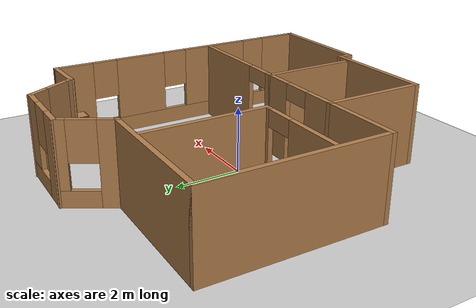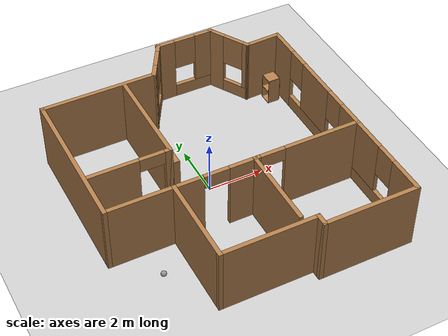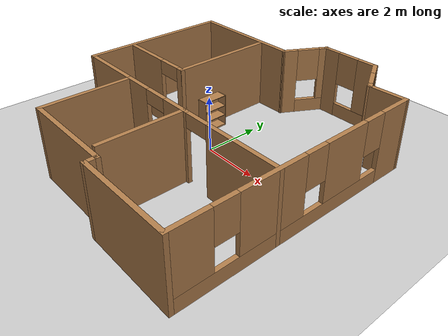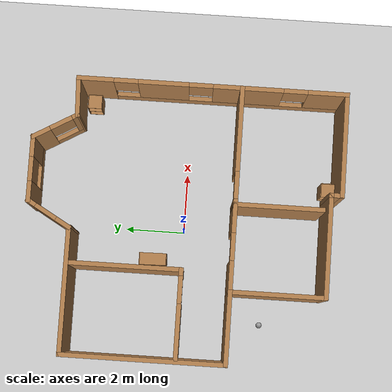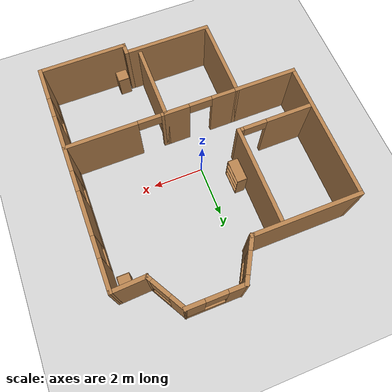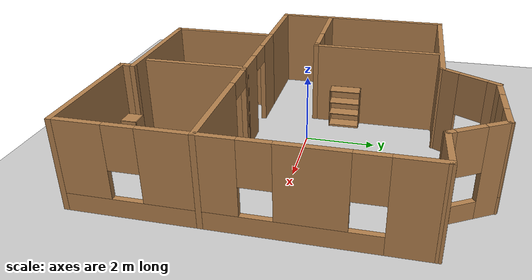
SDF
<sdf version="1.6">
 <world name="default">
  <light name="sun" type="directional">
   <pose>0 0 15 0 -0 0</pose>
   <diffuse>1 1 1 1</diffuse>
   <specular>0.1 0.1 0.1 1</specular>
   <attenuation>
    <range>1000</range>
    <constant>0.9</constant>
    <linear>0.01</linear>
    <quadratic>0.001</quadratic>
   </attenuation>
   <direction>-0.5 0.5 -1</direction>
  </light>
  <model name="ground_plane">
   <static>1</static>
   <link name="link">
    <collision name="collision">
     <geometry><plane><normal>0 0 1</normal><size>100 100</size></plane></geometry>
     <surface><friction><ode><mu>100</mu><mu2>50</mu2></ode></friction></surface>
    </collision>
    <visual name="visual">
     <cast_shadows>0</cast_shadows>
     <geometry><plane><normal>0 0 1</normal><size>100 100</size></plane></geometry>
     <material>
      <script><uri>file://media/materials/scripts/gazebo.material</uri><name>Gazebo/Grey</name></script>
     </material>
    </visual>
   </link>
  </model>
  <gravity>0 0 -9.8</gravity>
  <magnetic_field>6e-06 2.3e-05 -4.2e-05</magnetic_field>
  <atmosphere type="adiabatic"/>
  <physics name="default_physics" default="0" type="ode">
   <max_step_size>0.001</max_step_size>
   <real_time_factor>1</real_time_factor>
   <real_time_update_rate>1000</real_time_update_rate>
  </physics>
  <scene><ambient>0.4 0.4 0.4 1</ambient><background>0.7 0.7 0.7 1</background><shadows>1</shadows></scene>
  <spherical_coordinates>
   <surface_model>EARTH_WGS84</surface_model>
   <latitude_deg>0</latitude_deg>
   <longitude_deg>0</longitude_deg>
   <elevation>0</elevation>
   <heading_deg>0</heading_deg>
  </spherical_coordinates>
  <model name="cabinet">
   <static>1</static>
   <link name="cabinet_bottom_plate">
    <inertial>
     <pose>0 0 -1 0 -0 0</pose>
     <inertia><ixx>2.05</ixx><ixy>0</ixy><ixz>0</ixz><iyy>2.05</iyy><iyz>0</iyz><izz>2.05</izz></inertia>
     <mass>25</mass>
    </inertial>
    <collision name="cabinet_bottom_plate_geom">
     <pose>0 0 0.01 0 -0 0</pose>
     <geometry><box><size>0.45 0.45 0.02</size></box></geometry>
    </collision>
    <visual name="cabinet_bottom_plate_geom_visual">
     <pose>0 0 0.01 0 -0 0</pose>
     <geometry><box><size>0.45 0.45 0.02</size></box></geometry>
     <material>
      <script><uri>file://media/materials/scripts/gazebo.material</uri><name>Gazebo/Wood</name></script>
     </material>
    </visual>
    <collision name="cabinet_bottom_plate_geom_cabinet_back_plate">
     <pose>0.235 0 0.51 0 -0 0</pose>
     <geometry><box><size>0.02 0.45 1.02</size></box></geometry>
    </collision>
    <visual name="cabinet_bottom_plate_geom_cabinet_back_plate_visual">
     <pose>0.235 0 0.51 0 -0 0</pose>
     <geometry><box><size>0.02 0.45 1.02</size></box></geometry>
     <material>
      <script><uri>file://media/materials/scripts/gazebo.material</uri><name>Gazebo/Wood</name></script>
     </material>
    </visual>
    <collision name="cabinet_bottom_plate_geom_cabinet_left_plate">
     <pose>0 0.235 0.51 0 -0 0</pose>
     <geometry><box><size>0.45 0.02 1.02</size></box></geometry>
    </collision>
    <visual name="cabinet_bottom_plate_geom_cabinet_left_plate_visual">
     <pose>0 0.235 0.51 0 -0 0</pose>
     <geometry><box><size>0.45 0.02 1.02</size></box></geometry>
     <material>
      <script><uri>file://media/materials/scripts/gazebo.material</uri><name>Gazebo/Wood</name></script>
     </material>
    </visual>
    <collision name="cabinet_bottom_plate_geom_cabinet_middle_plate">
     <pose>0 0 0.51 0 -0 0</pose>
     <geometry><box><size>0.45 0.45 0.02</size></box></geometry>
    </collision>
    <visual name="cabinet_bottom_plate_geom_cabinet_middle_plate_visual">
     <pose>0 0 0.51 0 -0 0</pose>
     <geometry><box><size>0.45 0.45 0.02</size></box></geometry>
     <material>
      <script><uri>file://media/materials/scripts/gazebo.material</uri><name>Gazebo/Wood</name></script>
     </material>
    </visual>
    <collision name="cabinet_bottom_plate_geom_cabinet_right_plate">
     <pose>0 -0.235 0.51 0 -0 0</pose>
     <geometry><box><size>0.45 0.02 1.02</size></box></geometry>
    </collision>
    <visual name="cabinet_bottom_plate_geom_cabinet_right_plate_visual">
     <pose>0 -0.235 0.51 0 -0 0</pose>
     <geometry><box><size>0.45 0.02 1.02</size></box></geometry>
     <material>
      <script><uri>file://media/materials/scripts/gazebo.material</uri><name>Gazebo/Wood</name></script>
     </material>
    </visual>
    <collision name="cabinet_bottom_plate_geom_cabinet_top_plate">
     <pose>0 0 1.01 0 -0 0</pose>
     <geometry><box><size>0.45 0.45 0.02</size></box></geometry>
    </collision>
    <visual name="cabinet_bottom_plate_geom_cabinet_top_plate_visual">
     <pose>0 0 1.01 0 -0 0</pose>
     <geometry><box><size>0.45 0.45 0.02</size></box></geometry>
     <material>
      <script><uri>file://media/materials/scripts/gazebo.material</uri><name>Gazebo/Wood</name></script>
     </material>
    </visual>
   </link>
   <pose>1.66738 -4.78154 0 0 -0 0</pose>
  </model>
  <model name="bookshelf">
   <static>1</static>
   <link name="link">
    <inertial><mass>1</mass></inertial>
    <collision name="back">
     <pose>0 0.005 0.6 0 -0 0</pose>
     <geometry><box><size>0.9 0.01 1.2</size></box></geometry>
    </collision>
    <visual name="visual1">
     <pose>0 0.005 0.6 0 -0 0</pose>
     <geometry><box><size>0.9 0.01 1.2</size></box></geometry>
     <material>
      <script><uri>file://media/materials/scripts/gazebo.material</uri><name>Gazebo/Wood</name></script>
     </material>
    </visual>
    <collision name="left_side">
     <pose>0.45 -0.195 0.6 0 -0 0</pose>
     <geometry><box><size>0.02 0.4 1.2</size></box></geometry>
    </collision>
    <visual name="visual2">
     <pose>0.45 -0.195 0.6 0 -0 0</pose>
     <geometry><box><size>0.02 0.4 1.2</size></box></geometry>
     <material>
      <script><uri>file://media/materials/scripts/gazebo.material</uri><name>Gazebo/Wood</name></script>
     </material>
    </visual>
    <collision name="right_side">
     <pose>-0.45 -0.195 0.6 0 -0 0</pose>
     <geometry><box><size>0.02 0.4 1.2</size></box></geometry>
    </collision>
    <visual name="visual3">
     <pose>-0.45 -0.195 0.6 0 -0 0</pose>
     <geometry><box><size>0.02 0.4 1.2</size></box></geometry>
     <material>
      <script><uri>file://media/materials/scripts/gazebo.material</uri><name>Gazebo/Wood</name></script>
     </material>
    </visual>
    <collision name="bottom">
     <pose>0 -0.195 0.03 0 -0 0</pose>
     <geometry><box><size>0.88 0.4 0.06</size></box></geometry>
    </collision>
    <visual name="visual4">
     <pose>0 -0.195 0.03 0 -0 0</pose>
     <geometry><box><size>0.88 0.4 0.06</size></box></geometry>
     <material>
      <script><uri>file://media/materials/scripts/gazebo.material</uri><name>Gazebo/Wood</name></script>
     </material>
    </visual>
    <collision name="top">
     <pose>0 -0.195 1.19 0 -0 0</pose>
     <geometry><box><size>0.88 0.4 0.02</size></box></geometry>
    </collision>
    <visual name="visual5">
     <pose>0 -0.195 1.19 0 -0 0</pose>
     <geometry><box><size>0.88 0.4 0.02</size></box></geometry>
     <material>
      <script><uri>file://media/materials/scripts/gazebo.material</uri><name>Gazebo/Wood</name></script>
     </material>
    </visual>
    <collision name="low_shelf">
     <pose>0 -0.195 0.43 0 -0 0</pose>
     <geometry><box><size>0.88 0.4 0.02</size></box></geometry>
    </collision>
    <visual name="visual6">
     <pose>0 -0.195 0.43 0 -0 0</pose>
     <geometry><box><size>0.88 0.4 0.02</size></box></geometry>
     <material>
      <script><uri>file://media/materials/scripts/gazebo.material</uri><name>Gazebo/Wood</name></script>
     </material>
    </visual>
    <collision name="high_shelf">
     <pose>0 -0.195 0.8 0 -0 0</pose>
     <geometry><box><size>0.88 0.4 0.02</size></box></geometry>
    </collision>
    <visual name="visual7">
     <pose>0 -0.195 0.8 0 -0 0</pose>
     <geometry><box><size>0.88 0.4 0.02</size></box></geometry>
     <material>
      <script><uri>file://media/materials/scripts/gazebo.material</uri><name>Gazebo/Wood</name></script>
     </material>
    </visual>
   </link>
   <pose>-1.24281 0.975028 0.065504 0 -0 1.58566</pose>
  </model>
  <model name="cabinet_0">
   <static>1</static>
   <link name="cabinet_bottom_plate">
    <inertial>
     <pose>0 0 -1 0 -0 0</pose>
     <inertia><ixx>2.05</ixx><ixy>0</ixy><ixz>0</ixz><iyy>2.05</iyy><iyz>0</iyz><izz>2.05</izz></inertia>
     <mass>25</mass>
    </inertial>
    <collision name="cabinet_bottom_plate_geom">
     <pose>0 0 0.01 0 -0 0</pose>
     <geometry><box><size>0.45 0.45 0.02</size></box></geometry>
    </collision>
    <visual name="cabinet_bottom_plate_geom_visual">
     <pose>0 0 0.01 0 -0 0</pose>
     <geometry><box><size>0.45 0.45 0.02</size></box></geometry>
     <material>
      <script><uri>file://media/materials/scripts/gazebo.material</uri><name>Gazebo/Wood</name></script>
     </material>
    </visual>
    <collision name="cabinet_bottom_plate_geom_cabinet_back_plate">
     <pose>0.235 0 0.51 0 -0 0</pose>
     <geometry><box><size>0.02 0.45 1.02</size></box></geometry>
    </collision>
    <visual name="cabinet_bottom_plate_geom_cabinet_back_plate_visual">
     <pose>0.235 0 0.51 0 -0 0</pose>
     <geometry><box><size>0.02 0.45 1.02</size></box></geometry>
     <material>
      <script><uri>file://media/materials/scripts/gazebo.material</uri><name>Gazebo/Wood</name></script>
     </material>
    </visual>
    <collision name="cabinet_bottom_plate_geom_cabinet_left_plate">
     <pose>0 0.235 0.51 0 -0 0</pose>
     <geometry><box><size>0.45 0.02 1.02</size></box></geometry>
    </collision>
    <visual name="cabinet_bottom_plate_geom_cabinet_left_plate_visual">
     <pose>0 0.235 0.51 0 -0 0</pose>
     <geometry><box><size>0.45 0.02 1.02</size></box></geometry>
     <material>
      <script><uri>file://media/materials/scripts/gazebo.material</uri><name>Gazebo/Wood</name></script>
     </material>
    </visual>
    <collision name="cabinet_bottom_plate_geom_cabinet_middle_plate">
     <pose>0 0 0.51 0 -0 0</pose>
     <geometry><box><size>0.45 0.45 0.02</size></box></geometry>
    </collision>
    <visual name="cabinet_bottom_plate_geom_cabinet_middle_plate_visual">
     <pose>0 0 0.51 0 -0 0</pose>
     <geometry><box><size>0.45 0.45 0.02</size></box></geometry>
     <material>
      <script><uri>file://media/materials/scripts/gazebo.material</uri><name>Gazebo/Wood</name></script>
     </material>
    </visual>
    <collision name="cabinet_bottom_plate_geom_cabinet_right_plate">
     <pose>0 -0.235 0.51 0 -0 0</pose>
     <geometry><box><size>0.45 0.02 1.02</size></box></geometry>
    </collision>
    <visual name="cabinet_bottom_plate_geom_cabinet_right_plate_visual">
     <pose>0 -0.235 0.51 0 -0 0</pose>
     <geometry><box><size>0.45 0.02 1.02</size></box></geometry>
     <material>
      <script><uri>file://media/materials/scripts/gazebo.material</uri><name>Gazebo/Wood</name></script>
     </material>
    </visual>
    <collision name="cabinet_bottom_plate_geom_cabinet_top_plate">
     <pose>0 0 1.01 0 -0 0</pose>
     <geometry><box><size>0.45 0.45 0.02</size></box></geometry>
    </collision>
    <visual name="cabinet_bottom_plate_geom_cabinet_top_plate_visual">
     <pose>0 0 1.01 0 -0 0</pose>
     <geometry><box><size>0.45 0.45 0.02</size></box></geometry>
     <material>
      <script><uri>file://media/materials/scripts/gazebo.material</uri><name>Gazebo/Wood</name></script>
     </material>
    </visual>
   </link>
   <pose>4.2117 3.31957 0 0 -0 0</pose>
  </model>
  <model name="badrs">
   <link name="Wall_21">
    <pose>4.52353 -0.681546 0 0 0 -1.5708</pose>
    <inertial>
     <mass>1</mass>
     <inertia><ixx>1</ixx><ixy>0</ixy><ixz>0</ixz><iyy>1</iyy><iyz>0</iyz><izz>1</izz></inertia>
    </inertial>
    <visual name="Wall_21_Visual_0">
     <pose>-3.88245 0 1.25 0 -0 0</pose>
     <geometry><box><size>1.2351 0.15 2.5</size></box></geometry>
     <material>
      <script><uri>file://media/materials/scripts/gazebo.material</uri><name>Gazebo/Wood</name></script>
      <ambient>1 1 1 1</ambient>
      <shader type="pixel"><normal_map>__default__</normal_map></shader>
      <diffuse>1 1 1 1</diffuse>
      <specular>0 0 0 1</specular>
      <emissive>0 0 0 1</emissive>
     </material>
     <meta><layer>0</layer></meta>
    </visual>
    <visual name="Wall_21_Visual_1">
     <pose>0.617551 0 0.25 0 -0 0</pose>
     <geometry><box><size>7.7649 0.15 0.5</size></box></geometry>
     <material>
      <script><uri>file://media/materials/scripts/gazebo.material</uri><name>Gazebo/Wood</name></script>
      <ambient>1 1 1 1</ambient>
      <shader type="pixel"><normal_map>__default__</normal_map></shader>
      <diffuse>1 1 1 1</diffuse>
      <specular>0 0 0 1</specular>
      <emissive>0 0 0 1</emissive>
     </material>
     <meta><layer>0</layer></meta>
    </visual>
    <visual name="Wall_21_Visual_2">
     <pose>-1.62599 0 1.5 0 -0 0</pose>
     <geometry><box><size>1.67781 0.15 2</size></box></geometry>
     <material>
      <script><uri>file://media/materials/scripts/gazebo.material</uri><name>Gazebo/Wood</name></script>
      <ambient>1 1 1 1</ambient>
      <shader type="pixel"><normal_map>__default__</normal_map></shader>
      <diffuse>1 1 1 1</diffuse>
      <specular>0 0 0 1</specular>
      <emissive>0 0 0 1</emissive>
     </material>
     <meta><layer>0</layer></meta>
    </visual>
    <visual name="Wall_21_Visual_3">
     <pose>1.17301 0 1.5 0 -0 0</pose>
     <geometry><box><size>2.3202 0.15 2</size></box></geometry>
     <material>
      <script><uri>file://media/materials/scripts/gazebo.material</uri><name>Gazebo/Wood</name></script>
      <ambient>1 1 1 1</ambient>
      <shader type="pixel"><normal_map>__default__</normal_map></shader>
      <diffuse>1 1 1 1</diffuse>
      <specular>0 0 0 1</specular>
      <emissive>0 0 0 1</emissive>
     </material>
     <meta><layer>0</layer></meta>
    </visual>
    <visual name="Wall_21_Visual_4">
     <pose>3.81656 0 1.5 0 -0 0</pose>
     <geometry><box><size>1.36689 0.15 2</size></box></geometry>
     <material>
      <script><uri>file://media/materials/scripts/gazebo.material</uri><name>Gazebo/Wood</name></script>
      <ambient>1 1 1 1</ambient>
      <shader type="pixel"><normal_map>__default__</normal_map></shader>
      <diffuse>1 1 1 1</diffuse>
      <specular>0 0 0 1</specular>
      <emissive>0 0 0 1</emissive>
     </material>
     <meta><layer>0</layer></meta>
    </visual>
    <visual name="Wall_21_Visual_5">
     <pose>-2.8649 0 1.9 0 -0 0</pose>
     <geometry><box><size>0.8 0.15 1.2</size></box></geometry>
     <material>
      <script><uri>file://media/materials/scripts/gazebo.material</uri><name>Gazebo/Wood</name></script>
      <ambient>1 1 1 1</ambient>
      <shader type="pixel"><normal_map>__default__</normal_map></shader>
      <diffuse>1 1 1 1</diffuse>
      <specular>0 0 0 1</specular>
      <emissive>0 0 0 1</emissive>
     </material>
     <meta><layer>0</layer></meta>
    </visual>
    <visual name="Wall_21_Visual_6">
     <pose>-0.38709 0 1.9 0 -0 0</pose>
     <geometry><box><size>0.8 0.15 1.2</size></box></geometry>
     <material>
      <script><uri>file://media/materials/scripts/gazebo.material</uri><name>Gazebo/Wood</name></script>
      <ambient>1 1 1 1</ambient>
      <shader type="pixel"><normal_map>__default__</normal_map></shader>
      <diffuse>1 1 1 1</diffuse>
      <specular>0 0 0 1</specular>
      <emissive>0 0 0 1</emissive>
     </material>
     <meta><layer>0</layer></meta>
    </visual>
    <visual name="Wall_21_Visual_7">
     <pose>2.73311 0 1.9 0 -0 0</pose>
     <geometry><box><size>0.8 0.15 1.2</size></box></geometry>
     <material>
      <script><uri>file://media/materials/scripts/gazebo.material</uri><name>Gazebo/Wood</name></script>
      <ambient>1 1 1 1</ambient>
      <shader type="pixel"><normal_map>__default__</normal_map></shader>
      <diffuse>1 1 1 1</diffuse>
      <specular>0 0 0 1</specular>
      <emissive>0 0 0 1</emissive>
     </material>
     <meta><layer>0</layer></meta>
    </visual>
    <collision name="Wall_21_Collision_0">
     <pose>-3.88245 0 1.25 0 -0 0</pose>
     <geometry><box><size>1.2351 0.15 2.5</size></box></geometry>
     <surface>
      <friction>
       <ode><mu>1</mu><mu2>1</mu2><fdir1>0 0 0</fdir1><slip1>0</slip1><slip2>0</slip2></ode>
       <torsional>
        <coefficient>1</coefficient>
        <patch_radius>0</patch_radius>
        <surface_radius>0</surface_radius>
        <use_patch_radius>1</use_patch_radius>
        <ode><slip>0</slip></ode>
       </torsional>
      </friction>
      <bounce><restitution_coefficient>0</restitution_coefficient><threshold>1e+06</threshold></bounce>
      <contact>
       <collide_without_contact>0</collide_without_contact>
       <collide_without_contact_bitmask>1</collide_without_contact_bitmask>
       <collide_bitmask>1</collide_bitmask>
       <ode>
        <soft_cfm>0</soft_cfm>
        <soft_erp>0.2</soft_erp>
        <kp>1e+13</kp>
        <kd>1</kd>
        <max_vel>0.01</max_vel>
        <min_depth>0</min_depth>
       </ode>
       <bullet>
        <split_impulse>1</split_impulse>
        <split_impulse_penetration_threshold>-0.01</split_impulse_penetration_threshold>
        <soft_cfm>0</soft_cfm>
        <soft_erp>0.2</soft_erp>
        <kp>1e+13</kp>
        <kd>1</kd>
       </bullet>
      </contact>
     </surface>
    </collision>
    <collision name="Wall_21_Collision_1">
     <pose>0.617551 0 0.25 0 -0 0</pose>
     <geometry><box><size>7.7649 0.15 0.5</size></box></geometry>
     <surface>
      <friction>
       <ode><mu>1</mu><mu2>1</mu2><fdir1>0 0 0</fdir1><slip1>0</slip1><slip2>0</slip2></ode>
       <torsional>
        <coefficient>1</coefficient>
        <patch_radius>0</patch_radius>
        <surface_radius>0</surface_radius>
        <use_patch_radius>1</use_patch_radius>
        <ode><slip>0</slip></ode>
       </torsional>
      </friction>
      <bounce><restitution_coefficient>0</restitution_coefficient><threshold>1e+06</threshold></bounce>
      <contact>
       <collide_without_contact>0</collide_without_contact>
       <collide_without_contact_bitmask>1</collide_without_contact_bitmask>
       <collide_bitmask>1</collide_bitmask>
       <ode>
        <soft_cfm>0</soft_cfm>
        <soft_erp>0.2</soft_erp>
        <kp>1e+13</kp>
        <kd>1</kd>
        <max_vel>0.01</max_vel>
        <min_depth>0</min_depth>
       </ode>
       <bullet>
        <split_impulse>1</split_impulse>
        <split_impulse_penetration_threshold>-0.01</split_impulse_penetration_threshold>
        <soft_cfm>0</soft_cfm>
        <soft_erp>0.2</soft_erp>
        <kp>1e+13</kp>
        <kd>1</kd>
       </bullet>
      </contact>
     </surface>
    </collision>
    <collision name="Wall_21_Collision_2">
     <pose>-1.62599 0 1.5 0 -0 0</pose>
     <geometry><box><size>1.67781 0.15 2</size></box></geometry>
     <surface>
      <friction>
       <ode><mu>1</mu><mu2>1</mu2><fdir1>0 0 0</fdir1><slip1>0</slip1><slip2>0</slip2></ode>
       <torsional>
        <coefficient>1</coefficient>
        <patch_radius>0</patch_radius>
        <surface_radius>0</surface_radius>
        <use_patch_radius>1</use_patch_radius>
        <ode><slip>0</slip></ode>
       </torsional>
      </friction>
      <bounce><restitution_coefficient>0</restitution_coefficient><threshold>1e+06</threshold></bounce>
      <contact>
       <collide_without_contact>0</collide_without_contact>
       <collide_without_contact_bitmask>1</collide_without_contact_bitmask>
       <collide_bitmask>1</collide_bitmask>
       <ode>
        <soft_cfm>0</soft_cfm>
        <soft_erp>0.2</soft_erp>
        <kp>1e+13</kp>
        <kd>1</kd>
        <max_vel>0.01</max_vel>
        <min_depth>0</min_depth>
       </ode>
       <bullet>
        <split_impulse>1</split_impulse>
        <split_impulse_penetration_threshold>-0.01</split_impulse_penetration_threshold>
        <soft_cfm>0</soft_cfm>
        <soft_erp>0.2</soft_erp>
        <kp>1e+13</kp>
        <kd>1</kd>
       </bullet>
      </contact>
     </surface>
    </collision>
    <collision name="Wall_21_Collision_3">
     <pose>1.17301 0 1.5 0 -0 0</pose>
     <geometry><box><size>2.3202 0.15 2</size></box></geometry>
     <surface>
      <friction>
       <ode><mu>1</mu><mu2>1</mu2><fdir1>0 0 0</fdir1><slip1>0</slip1><slip2>0</slip2></ode>
       <torsional>
        <coefficient>1</coefficient>
        <patch_radius>0</patch_radius>
        <surface_radius>0</surface_radius>
        <use_patch_radius>1</use_patch_radius>
        <ode><slip>0</slip></ode>
       </torsional>
      </friction>
      <bounce><restitution_coefficient>0</restitution_coefficient><threshold>1e+06</threshold></bounce>
      <contact>
       <collide_without_contact>0</collide_without_contact>
       <collide_without_contact_bitmask>1</collide_without_contact_bitmask>
       <collide_bitmask>1</collide_bitmask>
       <ode>
        <soft_cfm>0</soft_cfm>
        <soft_erp>0.2</soft_erp>
        <kp>1e+13</kp>
        <kd>1</kd>
        <max_vel>0.01</max_vel>
        <min_depth>0</min_depth>
       </ode>
       <bullet>
        <split_impulse>1</split_impulse>
        <split_impulse_penetration_threshold>-0.01</split_impulse_penetration_threshold>
        <soft_cfm>0</soft_cfm>
        <soft_erp>0.2</soft_erp>
        <kp>1e+13</kp>
        <kd>1</kd>
       </bullet>
      </contact>
     </surface>
    </collision>
    <collision name="Wall_21_Collision_4">
     <pose>3.81656 0 1.5 0 -0 0</pose>
     <geometry><box><size>1.36689 0.15 2</size></box></geometry>
     <surface>
      <friction>
       <ode><mu>1</mu><mu2>1</mu2><fdir1>0 0 0</fdir1><slip1>0</slip1><slip2>0</slip2></ode>
       <torsional>
        <coefficient>1</coefficient>
        <patch_radius>0</patch_radius>
        <surface_radius>0</surface_radius>
        <use_patch_radius>1</use_patch_radius>
        <ode><slip>0</slip></ode>
       </torsional>
      </friction>
      <bounce><restitution_coefficient>0</restitution_coefficient><threshold>1e+06</threshold></bounce>
      <contact>
       <collide_without_contact>0</collide_without_contact>
       <collide_without_contact_bitmask>1</collide_without_contact_bitmask>
       <collide_bitmask>1</collide_bitmask>
       <ode>
        <soft_cfm>0</soft_cfm>
        <soft_erp>0.2</soft_erp>
        <kp>1e+13</kp>
        <kd>1</kd>
        <max_vel>0.01</max_vel>
        <min_depth>0</min_depth>
       </ode>
       <bullet>
        <split_impulse>1</split_impulse>
        <split_impulse_penetration_threshold>-0.01</split_impulse_penetration_threshold>
        <soft_cfm>0</soft_cfm>
        <soft_erp>0.2</soft_erp>
        <kp>1e+13</kp>
        <kd>1</kd>
       </bullet>
      </contact>
     </surface>
    </collision>
    <collision name="Wall_21_Collision_6">
     <pose>-0.38709 0 1.9 0 -0 0</pose>
     <geometry><box><size>0.8 0.15 1.2</size></box></geometry>
     <surface>
      <friction>
       <ode><mu>1</mu><mu2>1</mu2><fdir1>0 0 0</fdir1><slip1>0</slip1><slip2>0</slip2></ode>
       <torsional>
        <coefficient>1</coefficient>
        <patch_radius>0</patch_radius>
        <surface_radius>0</surface_radius>
        <use_patch_radius>1</use_patch_radius>
        <ode><slip>0</slip></ode>
       </torsional>
      </friction>
      <bounce><restitution_coefficient>0</restitution_coefficient><threshold>1e+06</threshold></bounce>
      <contact>
       <collide_without_contact>0</collide_without_contact>
       <collide_without_contact_bitmask>1</collide_without_contact_bitmask>
       <collide_bitmask>1</collide_bitmask>
       <ode>
        <soft_cfm>0</soft_cfm>
        <soft_erp>0.2</soft_erp>
        <kp>1e+13</kp>
        <kd>1</kd>
        <max_vel>0.01</max_vel>
        <min_depth>0</min_depth>
       </ode>
       <bullet>
        <split_impulse>1</split_impulse>
        <split_impulse_penetration_threshold>-0.01</split_impulse_penetration_threshold>
        <soft_cfm>0</soft_cfm>
        <soft_erp>0.2</soft_erp>
        <kp>1e+13</kp>
        <kd>1</kd>
       </bullet>
      </contact>
     </surface>
    </collision>
    <collision name="Wall_21_Collision_5">
     <pose>-2.8649 0 1.9 0 -0 0</pose>
     <geometry><box><size>0.8 0.15 1.2</size></box></geometry>
     <surface>
      <friction>
       <ode><mu>1</mu><mu2>1</mu2><fdir1>0 0 0</fdir1><slip1>0</slip1><slip2>0</slip2></ode>
       <torsional>
        <coefficient>1</coefficient>
        <patch_radius>0</patch_radius>
        <surface_radius>0</surface_radius>
        <use_patch_radius>1</use_patch_radius>
        <ode><slip>0</slip></ode>
       </torsional>
      </friction>
      <bounce><restitution_coefficient>0</restitution_coefficient><threshold>1e+06</threshold></bounce>
      <contact>
       <collide_without_contact>0</collide_without_contact>
       <collide_without_contact_bitmask>1</collide_without_contact_bitmask>
       <collide_bitmask>1</collide_bitmask>
       <ode>
        <soft_cfm>0</soft_cfm>
        <soft_erp>0.2</soft_erp>
        <kp>1e+13</kp>
        <kd>1</kd>
        <max_vel>0.01</max_vel>
        <min_depth>0</min_depth>
       </ode>
       <bullet>
        <split_impulse>1</split_impulse>
        <split_impulse_penetration_threshold>-0.01</split_impulse_penetration_threshold>
        <soft_cfm>0</soft_cfm>
        <soft_erp>0.2</soft_erp>
        <kp>1e+13</kp>
        <kd>1</kd>
       </bullet>
      </contact>
     </surface>
    </collision>
    <collision name="Wall_21_Collision_7">
     <pose>2.73311 0 1.9 0 -0 0</pose>
     <geometry><box><size>0.8 0.15 1.2</size></box></geometry>
     <surface>
      <friction>
       <ode><mu>1</mu><mu2>1</mu2><fdir1>0 0 0</fdir1><slip1>0</slip1><slip2>0</slip2></ode>
       <torsional>
        <coefficient>1</coefficient>
        <patch_radius>0</patch_radius>
        <surface_radius>0</surface_radius>
        <use_patch_radius>1</use_patch_radius>
        <ode><slip>0</slip></ode>
       </torsional>
      </friction>
      <bounce><restitution_coefficient>0</restitution_coefficient><threshold>1e+06</threshold></bounce>
      <contact>
       <collide_without_contact>0</collide_without_contact>
       <collide_without_contact_bitmask>1</collide_without_contact_bitmask>
       <collide_bitmask>1</collide_bitmask>
       <ode>
        <soft_cfm>0</soft_cfm>
        <soft_erp>0.2</soft_erp>
        <kp>1e+13</kp>
        <kd>1</kd>
        <max_vel>0.01</max_vel>
        <min_depth>0</min_depth>
       </ode>
       <bullet>
        <split_impulse>1</split_impulse>
        <split_impulse_penetration_threshold>-0.01</split_impulse_penetration_threshold>
        <soft_cfm>0</soft_cfm>
        <soft_erp>0.2</soft_erp>
        <kp>1e+13</kp>
        <kd>1</kd>
       </bullet>
      </contact>
     </surface>
    </collision>
   </link>
   <link name="Wall_22">
    <pose>2.84853 -5.10655 0 0 -0 3.14159</pose>
    <inertial>
     <mass>1</mass>
     <inertia><ixx>1</ixx><ixy>0</ixy><ixz>0</ixz><iyy>1</iyy><iyz>0</iyz><izz>1</izz></inertia>
    </inertial>
    <visual name="Wall_22_Visual">
     <pose>0 0 1.25 0 -0 0</pose>
     <geometry><box><size>3.5 0.15 2.5</size></box></geometry>
     <material>
      <script><uri>file://media/materials/scripts/gazebo.material</uri><name>Gazebo/Wood</name></script>
      <ambient>1 1 1 1</ambient>
      <shader type="pixel"><normal_map>__default__</normal_map></shader>
      <diffuse>1 1 1 1</diffuse>
      <specular>0 0 0 1</specular>
      <emissive>0 0 0 1</emissive>
     </material>
     <meta><layer>0</layer></meta>
    </visual>
    <collision name="Wall_22_Collision">
     <pose>0 0 1.25 0 -0 0</pose>
     <geometry><box><size>3.5 0.15 2.5</size></box></geometry>
     <surface>
      <friction>
       <ode><mu>1</mu><mu2>1</mu2><fdir1>0 0 0</fdir1><slip1>0</slip1><slip2>0</slip2></ode>
       <torsional>
        <coefficient>1</coefficient>
        <patch_radius>0</patch_radius>
        <surface_radius>0</surface_radius>
        <use_patch_radius>1</use_patch_radius>
        <ode><slip>0</slip></ode>
       </torsional>
      </friction>
      <bounce><restitution_coefficient>0</restitution_coefficient><threshold>1e+06</threshold></bounce>
      <contact>
       <collide_without_contact>0</collide_without_contact>
       <collide_without_contact_bitmask>1</collide_without_contact_bitmask>
       <collide_bitmask>1</collide_bitmask>
       <ode>
        <soft_cfm>0</soft_cfm>
        <soft_erp>0.2</soft_erp>
        <kp>1e+13</kp>
        <kd>1</kd>
        <max_vel>0.01</max_vel>
        <min_depth>0</min_depth>
       </ode>
       <bullet>
        <split_impulse>1</split_impulse>
        <split_impulse_penetration_threshold>-0.01</split_impulse_penetration_threshold>
        <soft_cfm>0</soft_cfm>
        <soft_erp>0.2</soft_erp>
        <kp>1e+13</kp>
        <kd>1</kd>
       </bullet>
      </contact>
     </surface>
    </collision>
   </link>
   <link name="Wall_23">
    <pose>1.17353 -4.93155 0 0 -0 1.5708</pose>
    <inertial>
     <mass>1</mass>
     <inertia><ixx>1</ixx><ixy>0</ixy><ixz>0</ixz><iyy>1</iyy><iyz>0</iyz><izz>1</izz></inertia>
    </inertial>
    <visual name="Wall_23_Visual">
     <pose>0 0 1.25 0 -0 0</pose>
     <geometry><box><size>0.5 0.15 2.5</size></box></geometry>
     <material>
      <script><uri>file://media/materials/scripts/gazebo.material</uri><name>Gazebo/Wood</name></script>
      <ambient>1 1 1 1</ambient>
      <shader type="pixel"><normal_map>__default__</normal_map></shader>
      <diffuse>0.7 0.7 0.7 1</diffuse>
      <specular>0.01 0.01 0.01 1</specular>
      <emissive>0 0 0 1</emissive>
     </material>
     <meta><layer>0</layer></meta>
    </visual>
    <collision name="Wall_23_Collision">
     <pose>0 0 1.25 0 -0 0</pose>
     <geometry><box><size>0.5 0.15 2.5</size></box></geometry>
     <surface>
      <friction>
       <ode><mu>1</mu><mu2>1</mu2><fdir1>0 0 0</fdir1><slip1>0</slip1><slip2>0</slip2></ode>
       <torsional>
        <coefficient>1</coefficient>
        <patch_radius>0</patch_radius>
        <surface_radius>0</surface_radius>
        <use_patch_radius>1</use_patch_radius>
        <ode><slip>0</slip></ode>
       </torsional>
      </friction>
      <bounce><restitution_coefficient>0</restitution_coefficient><threshold>1e+06</threshold></bounce>
      <contact>
       <collide_without_contact>0</collide_without_contact>
       <collide_without_contact_bitmask>1</collide_without_contact_bitmask>
       <collide_bitmask>1</collide_bitmask>
       <ode>
        <soft_cfm>0</soft_cfm>
        <soft_erp>0.2</soft_erp>
        <kp>1e+13</kp>
        <kd>1</kd>
        <max_vel>0.01</max_vel>
        <min_depth>0</min_depth>
       </ode>
       <bullet>
        <split_impulse>1</split_impulse>
        <split_impulse_penetration_threshold>-0.01</split_impulse_penetration_threshold>
        <soft_cfm>0</soft_cfm>
        <soft_erp>0.2</soft_erp>
        <kp>1e+13</kp>
        <kd>1</kd>
       </bullet>
      </contact>
     </surface>
    </collision>
   </link>
   <link name="Wall_24">
    <pose>-0.501469 -4.75655 0 0 -0 3.14159</pose>
    <inertial>
     <mass>1</mass>
     <inertia><ixx>1</ixx><ixy>0</ixy><ixz>0</ixz><iyy>1</iyy><iyz>0</iyz><izz>1</izz></inertia>
    </inertial>
    <visual name="Wall_24_Visual">
     <pose>0 0 1.25 0 -0 0</pose>
     <geometry><box><size>3.5 0.15 2.5</size></box></geometry>
     <material>
      <script><uri>file://media/materials/scripts/gazebo.material</uri><name>Gazebo/Wood</name></script>
      <ambient>1 1 1 1</ambient>
      <shader type="pixel"><normal_map>__default__</normal_map></shader>
      <diffuse>1 1 1 1</diffuse>
      <specular>0 0 0 1</specular>
      <emissive>0 0 0 1</emissive>
     </material>
     <meta><layer>0</layer></meta>
    </visual>
    <collision name="Wall_24_Collision">
     <pose>0 0 1.25 0 -0 0</pose>
     <geometry><box><size>3.5 0.15 2.5</size></box></geometry>
     <surface>
      <friction>
       <ode><mu>1</mu><mu2>1</mu2><fdir1>0 0 0</fdir1><slip1>0</slip1><slip2>0</slip2></ode>
       <torsional>
        <coefficient>1</coefficient>
        <patch_radius>0</patch_radius>
        <surface_radius>0</surface_radius>
        <use_patch_radius>1</use_patch_radius>
        <ode><slip>0</slip></ode>
       </torsional>
      </friction>
      <bounce><restitution_coefficient>0</restitution_coefficient><threshold>1e+06</threshold></bounce>
      <contact>
       <collide_without_contact>0</collide_without_contact>
       <collide_without_contact_bitmask>1</collide_without_contact_bitmask>
       <collide_bitmask>1</collide_bitmask>
       <ode>
        <soft_cfm>0</soft_cfm>
        <soft_erp>0.2</soft_erp>
        <kp>1e+13</kp>
        <kd>1</kd>
        <max_vel>0.01</max_vel>
        <min_depth>0</min_depth>
       </ode>
       <bullet>
        <split_impulse>1</split_impulse>
        <split_impulse_penetration_threshold>-0.01</split_impulse_penetration_threshold>
        <soft_cfm>0</soft_cfm>
        <soft_erp>0.2</soft_erp>
        <kp>1e+13</kp>
        <kd>1</kd>
       </bullet>
      </contact>
     </surface>
    </collision>
   </link>
   <link name="Wall_25">
    <pose>-2.17647 -3.20655 0 0 -0 1.5708</pose>
    <inertial>
     <mass>1</mass>
     <inertia><ixx>1</ixx><ixy>0</ixy><ixz>0</ixz><iyy>1</iyy><iyz>0</iyz><izz>1</izz></inertia>
    </inertial>
    <visual name="Wall_25_Visual">
     <pose>0 0 1.25 0 -0 0</pose>
     <geometry><box><size>3.25 0.15 2.5</size></box></geometry>
     <material>
      <script><uri>file://media/materials/scripts/gazebo.material</uri><name>Gazebo/Wood</name></script>
      <ambient>1 1 1 1</ambient>
      <shader type="pixel"><normal_map>__default__</normal_map></shader>
      <diffuse>0.7 0.7 0.7 1</diffuse>
      <specular>0.01 0.01 0.01 1</specular>
      <emissive>0 0 0 1</emissive>
     </material>
     <meta><layer>0</layer></meta>
    </visual>
    <collision name="Wall_25_Collision">
     <pose>0 0 1.25 0 -0 0</pose>
     <geometry><box><size>3.25 0.15 2.5</size></box></geometry>
     <surface>
      <friction>
       <ode><mu>1</mu><mu2>1</mu2><fdir1>0 0 0</fdir1><slip1>0</slip1><slip2>0</slip2></ode>
       <torsional>
        <coefficient>1</coefficient>
        <patch_radius>0</patch_radius>
        <surface_radius>0</surface_radius>
        <use_patch_radius>1</use_patch_radius>
        <ode><slip>0</slip></ode>
       </torsional>
      </friction>
      <bounce><restitution_coefficient>0</restitution_coefficient><threshold>1e+06</threshold></bounce>
      <contact>
       <collide_without_contact>0</collide_without_contact>
       <collide_without_contact_bitmask>1</collide_without_contact_bitmask>
       <collide_bitmask>1</collide_bitmask>
       <ode>
        <soft_cfm>0</soft_cfm>
        <soft_erp>0.2</soft_erp>
        <kp>1e+13</kp>
        <kd>1</kd>
        <max_vel>0.01</max_vel>
        <min_depth>0</min_depth>
       </ode>
       <bullet>
        <split_impulse>1</split_impulse>
        <split_impulse_penetration_threshold>-0.01</split_impulse_penetration_threshold>
        <soft_cfm>0</soft_cfm>
        <soft_erp>0.2</soft_erp>
        <kp>1e+13</kp>
        <kd>1</kd>
       </bullet>
      </contact>
     </surface>
    </collision>
   </link>
   <link name="Wall_26">
    <pose>-0.751469 -1.65655 0 0 -0 0</pose>
    <inertial>
     <mass>1</mass>
     <inertia><ixx>1</ixx><ixy>0</ixy><ixz>0</ixz><iyy>1</iyy><iyz>0</iyz><izz>1</izz></inertia>
    </inertial>
    <visual name="Wall_26_Visual_0">
     <pose>-0.952965 0 1.25 0 -0 0</pose>
     <geometry><box><size>1.09407 0.15 2.5</size></box></geometry>
     <material>
      <script><uri>file://media/materials/scripts/gazebo.material</uri><name>Gazebo/Wood</name></script>
      <ambient>1 1 1 1</ambient>
      <shader type="pixel"><normal_map>__default__</normal_map></shader>
      <diffuse>1 1 1 1</diffuse>
      <specular>0.2 0.2 0.2 1</specular>
      <emissive>0 0 0 1</emissive>
     </material>
     <meta><layer>0</layer></meta>
    </visual>
    <visual name="Wall_26_Visual_1">
     <pose>0.997035 0 1.25 0 -0 0</pose>
     <geometry><box><size>1.00593 0.15 2.5</size></box></geometry>
     <material>
      <script><uri>file://media/materials/scripts/gazebo.material</uri><name>Gazebo/Wood</name></script>
      <ambient>1 1 1 1</ambient>
      <shader type="pixel"><normal_map>__default__</normal_map></shader>
      <diffuse>1 1 1 1</diffuse>
      <specular>0.2 0.2 0.2 1</specular>
      <emissive>0 0 0 1</emissive>
     </material>
     <meta><layer>0</layer></meta>
    </visual>
    <visual name="Wall_26_Visual_2">
     <pose>0.044071 0 2.25 0 -0 0</pose>
     <geometry><box><size>0.9 0.15 0.5</size></box></geometry>
     <material>
      <script><uri>file://media/materials/scripts/gazebo.material</uri><name>Gazebo/Wood</name></script>
      <ambient>1 1 1 1</ambient>
      <shader type="pixel"><normal_map>__default__</normal_map></shader>
      <diffuse>1 1 1 1</diffuse>
      <specular>0.2 0.2 0.2 1</specular>
      <emissive>0 0 0 1</emissive>
     </material>
     <meta><layer>0</layer></meta>
    </visual>
    <collision name="Wall_26_Collision_2">
     <pose>0.044071 0 2.25 0 -0 0</pose>
     <geometry><box><size>0.9 0.15 0.5</size></box></geometry>
     <surface>
      <friction>
       <ode><mu>1</mu><mu2>1</mu2><fdir1>0 0 0</fdir1><slip1>0</slip1><slip2>0</slip2></ode>
       <torsional>
        <coefficient>1</coefficient>
        <patch_radius>0</patch_radius>
        <surface_radius>0</surface_radius>
        <use_patch_radius>1</use_patch_radius>
        <ode><slip>0</slip></ode>
       </torsional>
      </friction>
      <bounce><restitution_coefficient>0</restitution_coefficient><threshold>1e+06</threshold></bounce>
      <contact>
       <collide_without_contact>0</collide_without_contact>
       <collide_without_contact_bitmask>1</collide_without_contact_bitmask>
       <collide_bitmask>1</collide_bitmask>
       <ode>
        <soft_cfm>0</soft_cfm>
        <soft_erp>0.2</soft_erp>
        <kp>1e+13</kp>
        <kd>1</kd>
        <max_vel>0.01</max_vel>
        <min_depth>0</min_depth>
       </ode>
       <bullet>
        <split_impulse>1</split_impulse>
        <split_impulse_penetration_threshold>-0.01</split_impulse_penetration_threshold>
        <soft_cfm>0</soft_cfm>
        <soft_erp>0.2</soft_erp>
        <kp>1e+13</kp>
        <kd>1</kd>
       </bullet>
      </contact>
     </surface>
    </collision>
    <collision name="Wall_26_Collision_0">
     <pose>-0.952965 0 1.25 0 -0 0</pose>
     <geometry><box><size>1.09407 0.15 2.5</size></box></geometry>
     <surface>
      <friction>
       <ode><mu>1</mu><mu2>1</mu2><fdir1>0 0 0</fdir1><slip1>0</slip1><slip2>0</slip2></ode>
       <torsional>
        <coefficient>1</coefficient>
        <patch_radius>0</patch_radius>
        <surface_radius>0</surface_radius>
        <use_patch_radius>1</use_patch_radius>
        <ode><slip>0</slip></ode>
       </torsional>
      </friction>
      <bounce><restitution_coefficient>0</restitution_coefficient><threshold>1e+06</threshold></bounce>
      <contact>
       <collide_without_contact>0</collide_without_contact>
       <collide_without_contact_bitmask>1</collide_without_contact_bitmask>
       <collide_bitmask>1</collide_bitmask>
       <ode>
        <soft_cfm>0</soft_cfm>
        <soft_erp>0.2</soft_erp>
        <kp>1e+13</kp>
        <kd>1</kd>
        <max_vel>0.01</max_vel>
        <min_depth>0</min_depth>
       </ode>
       <bullet>
        <split_impulse>1</split_impulse>
        <split_impulse_penetration_threshold>-0.01</split_impulse_penetration_threshold>
        <soft_cfm>0</soft_cfm>
        <soft_erp>0.2</soft_erp>
        <kp>1e+13</kp>
        <kd>1</kd>
       </bullet>
      </contact>
     </surface>
    </collision>
    <collision name="Wall_26_Collision_1">
     <pose>0.997035 0 1.25 0 -0 0</pose>
     <geometry><box><size>1.00593 0.15 2.5</size></box></geometry>
     <surface>
      <friction>
       <ode><mu>1</mu><mu2>1</mu2><fdir1>0 0 0</fdir1><slip1>0</slip1><slip2>0</slip2></ode>
       <torsional>
        <coefficient>1</coefficient>
        <patch_radius>0</patch_radius>
        <surface_radius>0</surface_radius>
        <use_patch_radius>1</use_patch_radius>
        <ode><slip>0</slip></ode>
       </torsional>
      </friction>
      <bounce><restitution_coefficient>0</restitution_coefficient><threshold>1e+06</threshold></bounce>
      <contact>
       <collide_without_contact>0</collide_without_contact>
       <collide_without_contact_bitmask>1</collide_without_contact_bitmask>
       <collide_bitmask>1</collide_bitmask>
       <ode>
        <soft_cfm>0</soft_cfm>
        <soft_erp>0.2</soft_erp>
        <kp>1e+13</kp>
        <kd>1</kd>
        <max_vel>0.01</max_vel>
        <min_depth>0</min_depth>
       </ode>
       <bullet>
        <split_impulse>1</split_impulse>
        <split_impulse_penetration_threshold>-0.01</split_impulse_penetration_threshold>
        <soft_cfm>0</soft_cfm>
        <soft_erp>0.2</soft_erp>
        <kp>1e+13</kp>
        <kd>1</kd>
       </bullet>
      </contact>
     </surface>
    </collision>
   </link>
   <link name="Wall_27">
    <pose>0.673531 -3.08155 0 0 0 -1.5708</pose>
    <inertial>
     <mass>1</mass>
     <inertia><ixx>1</ixx><ixy>0</ixy><ixz>0</ixz><iyy>1</iyy><iyz>0</iyz><izz>1</izz></inertia>
    </inertial>
    <visual name="Wall_27_Visual">
     <pose>0 0 1.25 0 -0 0</pose>
     <geometry><box><size>3 0.15 2.5</size></box></geometry>
     <material>
      <script><uri>file://media/materials/scripts/gazebo.material</uri><name>Gazebo/Wood</name></script>
      <ambient>1 1 1 1</ambient>
      <shader type="pixel"><normal_map>__default__</normal_map></shader>
      <diffuse>1 1 1 1</diffuse>
      <specular>0.2 0.2 0.2 1</specular>
      <emissive>0 0 0 1</emissive>
     </material>
     <meta><layer>0</layer></meta>
    </visual>
    <collision name="Wall_27_Collision">
     <pose>0 0 1.25 0 -0 0</pose>
     <geometry><box><size>3 0.15 2.5</size></box></geometry>
     <surface>
      <friction>
       <ode><mu>1</mu><mu2>1</mu2><fdir1>0 0 0</fdir1><slip1>0</slip1><slip2>0</slip2></ode>
       <torsional>
        <coefficient>1</coefficient>
        <patch_radius>0</patch_radius>
        <surface_radius>0</surface_radius>
        <use_patch_radius>1</use_patch_radius>
        <ode><slip>0</slip></ode>
       </torsional>
      </friction>
      <bounce><restitution_coefficient>0</restitution_coefficient><threshold>1e+06</threshold></bounce>
      <contact>
       <collide_without_contact>0</collide_without_contact>
       <collide_without_contact_bitmask>1</collide_without_contact_bitmask>
       <collide_bitmask>1</collide_bitmask>
       <ode>
        <soft_cfm>0</soft_cfm>
        <soft_erp>0.2</soft_erp>
        <kp>1e+13</kp>
        <kd>1</kd>
        <max_vel>0.01</max_vel>
        <min_depth>0</min_depth>
       </ode>
       <bullet>
        <split_impulse>1</split_impulse>
        <split_impulse_penetration_threshold>-0.01</split_impulse_penetration_threshold>
        <soft_cfm>0</soft_cfm>
        <soft_erp>0.2</soft_erp>
        <kp>1e+13</kp>
        <kd>1</kd>
       </bullet>
      </contact>
     </surface>
    </collision>
   </link>
   <link name="Wall_29">
    <pose>-3.35147 -1.65655 0 0 -0 3.14159</pose>
    <inertial>
     <mass>1</mass>
     <inertia><ixx>1</ixx><ixy>0</ixy><ixz>0</ixz><iyy>1</iyy><iyz>0</iyz><izz>1</izz></inertia>
    </inertial>
    <visual name="Wall_29_Visual">
     <pose>0 0 1.25 0 -0 0</pose>
     <geometry><box><size>2.5 0.15 2.5</size></box></geometry>
     <material>
      <script><uri>file://media/materials/scripts/gazebo.material</uri><name>Gazebo/Wood</name></script>
      <ambient>1 1 1 1</ambient>
      <shader type="pixel"><normal_map>__default__</normal_map></shader>
      <diffuse>1 1 1 1</diffuse>
      <specular>0.2 0.2 0.2 1</specular>
      <emissive>0 0 0 1</emissive>
     </material>
     <meta><layer>0</layer></meta>
    </visual>
    <collision name="Wall_29_Collision">
     <pose>0 0 1.25 0 -0 0</pose>
     <geometry><box><size>2.5 0.15 2.5</size></box></geometry>
     <surface>
      <friction>
       <ode><mu>1</mu><mu2>1</mu2><fdir1>0 0 0</fdir1><slip1>0</slip1><slip2>0</slip2></ode>
       <torsional>
        <coefficient>1</coefficient>
        <patch_radius>0</patch_radius>
        <surface_radius>0</surface_radius>
        <use_patch_radius>1</use_patch_radius>
        <ode><slip>0</slip></ode>
       </torsional>
      </friction>
      <bounce><restitution_coefficient>0</restitution_coefficient><threshold>1e+06</threshold></bounce>
      <contact>
       <collide_without_contact>0</collide_without_contact>
       <collide_without_contact_bitmask>1</collide_without_contact_bitmask>
       <collide_bitmask>1</collide_bitmask>
       <ode>
        <soft_cfm>0</soft_cfm>
        <soft_erp>0.2</soft_erp>
        <kp>1e+13</kp>
        <kd>1</kd>
        <max_vel>0.01</max_vel>
        <min_depth>0</min_depth>
       </ode>
       <bullet>
        <split_impulse>1</split_impulse>
        <split_impulse_penetration_threshold>-0.01</split_impulse_penetration_threshold>
        <soft_cfm>0</soft_cfm>
        <soft_erp>0.2</soft_erp>
        <kp>1e+13</kp>
        <kd>1</kd>
       </bullet>
      </contact>
     </surface>
    </collision>
   </link>
   <link name="Wall_30">
    <pose>-4.52647 1.01845 0 0 -0 1.5708</pose>
    <inertial>
     <mass>1</mass>
     <inertia><ixx>1</ixx><ixy>0</ixy><ixz>0</ixz><iyy>1</iyy><iyz>0</iyz><izz>1</izz></inertia>
    </inertial>
    <visual name="Wall_30_Visual">
     <pose>0 0 1.25 0 -0 0</pose>
     <geometry><box><size>5.5 0.15 2.5</size></box></geometry>
     <material>
      <script><uri>file://media/materials/scripts/gazebo.material</uri><name>Gazebo/Wood</name></script>
      <ambient>1 1 1 1</ambient>
      <shader type="pixel"><normal_map>__default__</normal_map></shader>
      <diffuse>1 1 1 1</diffuse>
      <specular>0 0 0 1</specular>
      <emissive>0 0 0 1</emissive>
     </material>
     <meta><layer>0</layer></meta>
    </visual>
    <collision name="Wall_30_Collision">
     <pose>0 0 1.25 0 -0 0</pose>
     <geometry><box><size>5.5 0.15 2.5</size></box></geometry>
     <surface>
      <friction>
       <ode><mu>1</mu><mu2>1</mu2><fdir1>0 0 0</fdir1><slip1>0</slip1><slip2>0</slip2></ode>
       <torsional>
        <coefficient>1</coefficient>
        <patch_radius>0</patch_radius>
        <surface_radius>0</surface_radius>
        <use_patch_radius>1</use_patch_radius>
        <ode><slip>0</slip></ode>
       </torsional>
      </friction>
      <bounce><restitution_coefficient>0</restitution_coefficient><threshold>1e+06</threshold></bounce>
      <contact>
       <collide_without_contact>0</collide_without_contact>
       <collide_without_contact_bitmask>1</collide_without_contact_bitmask>
       <collide_bitmask>1</collide_bitmask>
       <ode>
        <soft_cfm>0</soft_cfm>
        <soft_erp>0.2</soft_erp>
        <kp>1e+13</kp>
        <kd>1</kd>
        <max_vel>0.01</max_vel>
        <min_depth>0</min_depth>
       </ode>
       <bullet>
        <split_impulse>1</split_impulse>
        <split_impulse_penetration_threshold>-0.01</split_impulse_penetration_threshold>
        <soft_cfm>0</soft_cfm>
        <soft_erp>0.2</soft_erp>
        <kp>1e+13</kp>
        <kd>1</kd>
       </bullet>
      </contact>
     </surface>
    </collision>
   </link>
   <link name="Wall_31">
    <pose>-2.47647 3.69345 0 0 -0 0</pose>
    <inertial>
     <mass>1</mass>
     <inertia><ixx>1</ixx><ixy>0</ixy><ixz>0</ixz><iyy>1</iyy><iyz>0</iyz><izz>1</izz></inertia>
    </inertial>
    <visual name="Wall_31_Visual">
     <pose>0 0 1.25 0 -0 0</pose>
     <geometry><box><size>4.25 0.15 2.5</size></box></geometry>
     <material>
      <script><uri>file://media/materials/scripts/gazebo.material</uri><name>Gazebo/Wood</name></script>
      <ambient>1 1 1 1</ambient>
      <shader type="pixel"><normal_map>__default__</normal_map></shader>
      <diffuse>1 1 1 1</diffuse>
      <specular>0 0 0 1</specular>
      <emissive>0 0 0 1</emissive>
     </material>
     <meta><layer>0</layer></meta>
    </visual>
    <collision name="Wall_31_Collision">
     <pose>0 0 1.25 0 -0 0</pose>
     <geometry><box><size>4.25 0.15 2.5</size></box></geometry>
     <surface>
      <friction>
       <ode><mu>1</mu><mu2>1</mu2><fdir1>0 0 0</fdir1><slip1>0</slip1><slip2>0</slip2></ode>
       <torsional>
        <coefficient>1</coefficient>
        <patch_radius>0</patch_radius>
        <surface_radius>0</surface_radius>
        <use_patch_radius>1</use_patch_radius>
        <ode><slip>0</slip></ode>
       </torsional>
      </friction>
      <bounce><restitution_coefficient>0</restitution_coefficient><threshold>1e+06</threshold></bounce>
      <contact>
       <collide_without_contact>0</collide_without_contact>
       <collide_without_contact_bitmask>1</collide_without_contact_bitmask>
       <collide_bitmask>1</collide_bitmask>
       <ode>
        <soft_cfm>0</soft_cfm>
        <soft_erp>0.2</soft_erp>
        <kp>1e+13</kp>
        <kd>1</kd>
        <max_vel>0.01</max_vel>
        <min_depth>0</min_depth>
       </ode>
       <bullet>
        <split_impulse>1</split_impulse>
        <split_impulse_penetration_threshold>-0.01</split_impulse_penetration_threshold>
        <soft_cfm>0</soft_cfm>
        <soft_erp>0.2</soft_erp>
        <kp>1e+13</kp>
        <kd>1</kd>
       </bullet>
      </contact>
     </surface>
    </collision>
   </link>
   <link name="Wall_32">
    <pose>-0.026469 4.38627 0 0 -0 1.0472</pose>
    <inertial>
     <mass>1</mass>
     <inertia><ixx>1</ixx><ixy>0</ixy><ixz>0</ixz><iyy>1</iyy><iyz>0</iyz><izz>1</izz></inertia>
    </inertial>
    <visual name="Wall_32_Visual_0">
     <pose>-0.584637 0 1.25 0 -0 0</pose>
     <geometry><box><size>0.580725 0.15 2.5</size></box></geometry>
     <material>
      <script><uri>file://media/materials/scripts/gazebo.material</uri><name>Gazebo/Wood</name></script>
      <ambient>1 1 1 1</ambient>
      <shader type="pixel"><normal_map>__default__</normal_map></shader>
      <diffuse>1 1 1 1</diffuse>
      <specular>0 0 0 1</specular>
      <emissive>0 0 0 1</emissive>
     </material>
     <meta><layer>0</layer></meta>
    </visual>
    <visual name="Wall_32_Visual_1">
     <pose>0.290363 0 0.25 0 -0 0</pose>
     <geometry><box><size>1.16928 0.15 0.5</size></box></geometry>
     <material>
      <script><uri>file://media/materials/scripts/gazebo.material</uri><name>Gazebo/Wood</name></script>
      <ambient>1 1 1 1</ambient>
      <shader type="pixel"><normal_map>__default__</normal_map></shader>
      <diffuse>1 1 1 1</diffuse>
      <specular>0 0 0 1</specular>
      <emissive>0 0 0 1</emissive>
     </material>
     <meta><layer>0</layer></meta>
    </visual>
    <visual name="Wall_32_Visual_2">
     <pose>0.690363 0 1.5 0 -0 0</pose>
     <geometry><box><size>0.369275 0.15 2</size></box></geometry>
     <material>
      <script><uri>file://media/materials/scripts/gazebo.material</uri><name>Gazebo/Wood</name></script>
      <ambient>1 1 1 1</ambient>
      <shader type="pixel"><normal_map>__default__</normal_map></shader>
      <diffuse>1 1 1 1</diffuse>
      <specular>0 0 0 1</specular>
      <emissive>0 0 0 1</emissive>
     </material>
     <meta><layer>0</layer></meta>
    </visual>
    <visual name="Wall_32_Visual_3">
     <pose>0.105725 0 1.9 0 -0 0</pose>
     <geometry><box><size>0.8 0.15 1.2</size></box></geometry>
     <material>
      <script><uri>file://media/materials/scripts/gazebo.material</uri><name>Gazebo/Wood</name></script>
      <ambient>1 1 1 1</ambient>
      <shader type="pixel"><normal_map>__default__</normal_map></shader>
      <diffuse>1 1 1 1</diffuse>
      <specular>0 0 0 1</specular>
      <emissive>0 0 0 1</emissive>
     </material>
     <meta><layer>0</layer></meta>
    </visual>
    <collision name="Wall_32_Collision_0">
     <pose>-0.584637 0 1.25 0 -0 0</pose>
     <geometry><box><size>0.580725 0.15 2.5</size></box></geometry>
     <surface>
      <friction>
       <ode><mu>1</mu><mu2>1</mu2><fdir1>0 0 0</fdir1><slip1>0</slip1><slip2>0</slip2></ode>
       <torsional>
        <coefficient>1</coefficient>
        <patch_radius>0</patch_radius>
        <surface_radius>0</surface_radius>
        <use_patch_radius>1</use_patch_radius>
        <ode><slip>0</slip></ode>
       </torsional>
      </friction>
      <bounce><restitution_coefficient>0</restitution_coefficient><threshold>1e+06</threshold></bounce>
      <contact>
       <collide_without_contact>0</collide_without_contact>
       <collide_without_contact_bitmask>1</collide_without_contact_bitmask>
       <collide_bitmask>1</collide_bitmask>
       <ode>
        <soft_cfm>0</soft_cfm>
        <soft_erp>0.2</soft_erp>
        <kp>1e+13</kp>
        <kd>1</kd>
        <max_vel>0.01</max_vel>
        <min_depth>0</min_depth>
       </ode>
       <bullet>
        <split_impulse>1</split_impulse>
        <split_impulse_penetration_threshold>-0.01</split_impulse_penetration_threshold>
        <soft_cfm>0</soft_cfm>
        <soft_erp>0.2</soft_erp>
        <kp>1e+13</kp>
        <kd>1</kd>
       </bullet>
      </contact>
     </surface>
    </collision>
    <collision name="Wall_32_Collision_1">
     <pose>0.290363 0 0.25 0 -0 0</pose>
     <geometry><box><size>1.16928 0.15 0.5</size></box></geometry>
     <surface>
      <friction>
       <ode><mu>1</mu><mu2>1</mu2><fdir1>0 0 0</fdir1><slip1>0</slip1><slip2>0</slip2></ode>
       <torsional>
        <coefficient>1</coefficient>
        <patch_radius>0</patch_radius>
        <surface_radius>0</surface_radius>
        <use_patch_radius>1</use_patch_radius>
        <ode><slip>0</slip></ode>
       </torsional>
      </friction>
      <bounce><restitution_coefficient>0</restitution_coefficient><threshold>1e+06</threshold></bounce>
      <contact>
       <collide_without_contact>0</collide_without_contact>
       <collide_without_contact_bitmask>1</collide_without_contact_bitmask>
       <collide_bitmask>1</collide_bitmask>
       <ode>
        <soft_cfm>0</soft_cfm>
        <soft_erp>0.2</soft_erp>
        <kp>1e+13</kp>
        <kd>1</kd>
        <max_vel>0.01</max_vel>
        <min_depth>0</min_depth>
       </ode>
       <bullet>
        <split_impulse>1</split_impulse>
        <split_impulse_penetration_threshold>-0.01</split_impulse_penetration_threshold>
        <soft_cfm>0</soft_cfm>
        <soft_erp>0.2</soft_erp>
        <kp>1e+13</kp>
        <kd>1</kd>
       </bullet>
      </contact>
     </surface>
    </collision>
    <collision name="Wall_32_Collision_2">
     <pose>0.690363 0 1.5 0 -0 0</pose>
     <geometry><box><size>0.369275 0.15 2</size></box></geometry>
     <surface>
      <friction>
       <ode><mu>1</mu><mu2>1</mu2><fdir1>0 0 0</fdir1><slip1>0</slip1><slip2>0</slip2></ode>
       <torsional>
        <coefficient>1</coefficient>
        <patch_radius>0</patch_radius>
        <surface_radius>0</surface_radius>
        <use_patch_radius>1</use_patch_radius>
        <ode><slip>0</slip></ode>
       </torsional>
      </friction>
      <bounce><restitution_coefficient>0</restitution_coefficient><threshold>1e+06</threshold></bounce>
      <contact>
       <collide_without_contact>0</collide_without_contact>
       <collide_without_contact_bitmask>1</collide_without_contact_bitmask>
       <collide_bitmask>1</collide_bitmask>
       <ode>
        <soft_cfm>0</soft_cfm>
        <soft_erp>0.2</soft_erp>
        <kp>1e+13</kp>
        <kd>1</kd>
        <max_vel>0.01</max_vel>
        <min_depth>0</min_depth>
       </ode>
       <bullet>
        <split_impulse>1</split_impulse>
        <split_impulse_penetration_threshold>-0.01</split_impulse_penetration_threshold>
        <soft_cfm>0</soft_cfm>
        <soft_erp>0.2</soft_erp>
        <kp>1e+13</kp>
        <kd>1</kd>
       </bullet>
      </contact>
     </surface>
    </collision>
    <collision name="Wall_32_Collision_3">
     <pose>0.105725 0 1.9 0 -0 0</pose>
     <geometry><box><size>0.8 0.15 1.2</size></box></geometry>
     <surface>
      <friction>
       <ode><mu>1</mu><mu2>1</mu2><fdir1>0 0 0</fdir1><slip1>0</slip1><slip2>0</slip2></ode>
       <torsional>
        <coefficient>1</coefficient>
        <patch_radius>0</patch_radius>
        <surface_radius>0</surface_radius>
        <use_patch_radius>1</use_patch_radius>
        <ode><slip>0</slip></ode>
       </torsional>
      </friction>
      <bounce><restitution_coefficient>0</restitution_coefficient><threshold>1e+06</threshold></bounce>
      <contact>
       <collide_without_contact>0</collide_without_contact>
       <collide_without_contact_bitmask>1</collide_without_contact_bitmask>
       <collide_bitmask>1</collide_bitmask>
       <ode>
        <soft_cfm>0</soft_cfm>
        <soft_erp>0.2</soft_erp>
        <kp>1e+13</kp>
        <kd>1</kd>
        <max_vel>0.01</max_vel>
        <min_depth>0</min_depth>
       </ode>
       <bullet>
        <split_impulse>1</split_impulse>
        <split_impulse_penetration_threshold>-0.01</split_impulse_penetration_threshold>
        <soft_cfm>0</soft_cfm>
        <soft_erp>0.2</soft_erp>
        <kp>1e+13</kp>
        <kd>1</kd>
       </bullet>
      </contact>
     </surface>
    </collision>
   </link>
   <link name="Wall_33">
    <pose>1.42353 5.07909 0 0 -0 0</pose>
    <inertial>
     <mass>1</mass>
     <inertia><ixx>1</ixx><ixy>0</ixy><ixz>0</ixz><iyy>1</iyy><iyz>0</iyz><izz>1</izz></inertia>
    </inertial>
    <visual name="Wall_33_Visual_0">
     <pose>-0.772602 0 1.25 0 -0 0</pose>
     <geometry><box><size>0.704797 0.15 2.5</size></box></geometry>
     <material>
      <script><uri>file://media/materials/scripts/gazebo.material</uri><name>Gazebo/Wood</name></script>
      <ambient>1 1 1 1</ambient>
      <shader type="pixel"><normal_map>__default__</normal_map></shader>
      <diffuse>1 1 1 1</diffuse>
      <specular>0 0 0 1</specular>
      <emissive>0 0 0 1</emissive>
     </material>
     <meta><layer>0</layer></meta>
    </visual>
    <visual name="Wall_33_Visual_1">
     <pose>0.352398 0 0.25 0 -0 0</pose>
     <geometry><box><size>1.5452 0.15 0.5</size></box></geometry>
     <material>
      <script><uri>file://media/materials/scripts/gazebo.material</uri><name>Gazebo/Wood</name></script>
      <ambient>1 1 1 1</ambient>
      <shader type="pixel"><normal_map>__default__</normal_map></shader>
      <diffuse>1 1 1 1</diffuse>
      <specular>0 0 0 1</specular>
      <emissive>0 0 0 1</emissive>
     </material>
     <meta><layer>0</layer></meta>
    </visual>
    <visual name="Wall_33_Visual_2">
     <pose>0.752398 0 1.5 0 -0 0</pose>
     <geometry><box><size>0.745203 0.15 2</size></box></geometry>
     <material>
      <script><uri>file://media/materials/scripts/gazebo.material</uri><name>Gazebo/Wood</name></script>
      <ambient>1 1 1 1</ambient>
      <shader type="pixel"><normal_map>__default__</normal_map></shader>
      <diffuse>1 1 1 1</diffuse>
      <specular>0 0 0 1</specular>
      <emissive>0 0 0 1</emissive>
     </material>
     <meta><layer>0</layer></meta>
    </visual>
    <visual name="Wall_33_Visual_3">
     <pose>-0.020203 0 1.9 0 -0 0</pose>
     <geometry><box><size>0.8 0.15 1.2</size></box></geometry>
     <material>
      <script><uri>file://media/materials/scripts/gazebo.material</uri><name>Gazebo/Wood</name></script>
      <ambient>1 1 1 1</ambient>
      <shader type="pixel"><normal_map>__default__</normal_map></shader>
      <diffuse>1 1 1 1</diffuse>
      <specular>0 0 0 1</specular>
      <emissive>0 0 0 1</emissive>
     </material>
     <meta><layer>0</layer></meta>
    </visual>
    <collision name="Wall_33_Collision_0">
     <pose>-0.772602 0 1.25 0 -0 0</pose>
     <geometry><box><size>0.704797 0.15 2.5</size></box></geometry>
     <surface>
      <friction>
       <ode><mu>1</mu><mu2>1</mu2><fdir1>0 0 0</fdir1><slip1>0</slip1><slip2>0</slip2></ode>
       <torsional>
        <coefficient>1</coefficient>
        <patch_radius>0</patch_radius>
        <surface_radius>0</surface_radius>
        <use_patch_radius>1</use_patch_radius>
        <ode><slip>0</slip></ode>
       </torsional>
      </friction>
      <bounce><restitution_coefficient>0</restitution_coefficient><threshold>1e+06</threshold></bounce>
      <contact>
       <collide_without_contact>0</collide_without_contact>
       <collide_without_contact_bitmask>1</collide_without_contact_bitmask>
       <collide_bitmask>1</collide_bitmask>
       <ode>
        <soft_cfm>0</soft_cfm>
        <soft_erp>0.2</soft_erp>
        <kp>1e+13</kp>
        <kd>1</kd>
        <max_vel>0.01</max_vel>
        <min_depth>0</min_depth>
       </ode>
       <bullet>
        <split_impulse>1</split_impulse>
        <split_impulse_penetration_threshold>-0.01</split_impulse_penetration_threshold>
        <soft_cfm>0</soft_cfm>
        <soft_erp>0.2</soft_erp>
        <kp>1e+13</kp>
        <kd>1</kd>
       </bullet>
      </contact>
     </surface>
    </collision>
    <collision name="Wall_33_Collision_3">
     <pose>-0.020203 0 1.9 0 -0 0</pose>
     <geometry><box><size>0.8 0.15 1.2</size></box></geometry>
     <surface>
      <friction>
       <ode><mu>1</mu><mu2>1</mu2><fdir1>0 0 0</fdir1><slip1>0</slip1><slip2>0</slip2></ode>
       <torsional>
        <coefficient>1</coefficient>
        <patch_radius>0</patch_radius>
        <surface_radius>0</surface_radius>
        <use_patch_radius>1</use_patch_radius>
        <ode><slip>0</slip></ode>
       </torsional>
      </friction>
      <bounce><restitution_coefficient>0</restitution_coefficient><threshold>1e+06</threshold></bounce>
      <contact>
       <collide_without_contact>0</collide_without_contact>
       <collide_without_contact_bitmask>1</collide_without_contact_bitmask>
       <collide_bitmask>1</collide_bitmask>
       <ode>
        <soft_cfm>0</soft_cfm>
        <soft_erp>0.2</soft_erp>
        <kp>1e+13</kp>
        <kd>1</kd>
        <max_vel>0.01</max_vel>
        <min_depth>0</min_depth>
       </ode>
       <bullet>
        <split_impulse>1</split_impulse>
        <split_impulse_penetration_threshold>-0.01</split_impulse_penetration_threshold>
        <soft_cfm>0</soft_cfm>
        <soft_erp>0.2</soft_erp>
        <kp>1e+13</kp>
        <kd>1</kd>
       </bullet>
      </contact>
     </surface>
    </collision>
    <collision name="Wall_33_Collision_1">
     <pose>0.352398 0 0.25 0 -0 0</pose>
     <geometry><box><size>1.5452 0.15 0.5</size></box></geometry>
     <surface>
      <friction>
       <ode><mu>1</mu><mu2>1</mu2><fdir1>0 0 0</fdir1><slip1>0</slip1><slip2>0</slip2></ode>
       <torsional>
        <coefficient>1</coefficient>
        <patch_radius>0</patch_radius>
        <surface_radius>0</surface_radius>
        <use_patch_radius>1</use_patch_radius>
        <ode><slip>0</slip></ode>
       </torsional>
      </friction>
      <bounce><restitution_coefficient>0</restitution_coefficient><threshold>1e+06</threshold></bounce>
      <contact>
       <collide_without_contact>0</collide_without_contact>
       <collide_without_contact_bitmask>1</collide_without_contact_bitmask>
       <collide_bitmask>1</collide_bitmask>
       <ode>
        <soft_cfm>0</soft_cfm>
        <soft_erp>0.2</soft_erp>
        <kp>1e+13</kp>
        <kd>1</kd>
        <max_vel>0.01</max_vel>
        <min_depth>0</min_depth>
       </ode>
       <bullet>
        <split_impulse>1</split_impulse>
        <split_impulse_penetration_threshold>-0.01</split_impulse_penetration_threshold>
        <soft_cfm>0</soft_cfm>
        <soft_erp>0.2</soft_erp>
        <kp>1e+13</kp>
        <kd>1</kd>
       </bullet>
      </contact>
     </surface>
    </collision>
    <collision name="Wall_33_Collision_2">
     <pose>0.752398 0 1.5 0 -0 0</pose>
     <geometry><box><size>0.745203 0.15 2</size></box></geometry>
     <surface>
      <friction>
       <ode><mu>1</mu><mu2>1</mu2><fdir1>0 0 0</fdir1><slip1>0</slip1><slip2>0</slip2></ode>
       <torsional>
        <coefficient>1</coefficient>
        <patch_radius>0</patch_radius>
        <surface_radius>0</surface_radius>
        <use_patch_radius>1</use_patch_radius>
        <ode><slip>0</slip></ode>
       </torsional>
      </friction>
      <bounce><restitution_coefficient>0</restitution_coefficient><threshold>1e+06</threshold></bounce>
      <contact>
       <collide_without_contact>0</collide_without_contact>
       <collide_without_contact_bitmask>1</collide_without_contact_bitmask>
       <collide_bitmask>1</collide_bitmask>
       <ode>
        <soft_cfm>0</soft_cfm>
        <soft_erp>0.2</soft_erp>
        <kp>1e+13</kp>
        <kd>1</kd>
        <max_vel>0.01</max_vel>
        <min_depth>0</min_depth>
       </ode>
       <bullet>
        <split_impulse>1</split_impulse>
        <split_impulse_penetration_threshold>-0.01</split_impulse_penetration_threshold>
        <soft_cfm>0</soft_cfm>
        <soft_erp>0.2</soft_erp>
        <kp>1e+13</kp>
        <kd>1</kd>
       </bullet>
      </contact>
     </surface>
    </collision>
   </link>
   <link name="Wall_34">
    <pose>2.87353 4.38627 0 0 0 -1.0472</pose>
    <inertial>
     <mass>1</mass>
     <inertia><ixx>1</ixx><ixy>0</ixy><ixz>0</ixz><iyy>1</iyy><iyz>0</iyz><izz>1</izz></inertia>
    </inertial>
    <visual name="Wall_34_Visual_0">
     <pose>-0.531816 0 1.25 0 -0 0</pose>
     <geometry><box><size>0.686368 0.15 2.5</size></box></geometry>
     <material>
      <script><uri>file://media/materials/scripts/gazebo.material</uri><name>Gazebo/Wood</name></script>
      <ambient>1 1 1 1</ambient>
      <shader type="pixel"><normal_map>__default__</normal_map></shader>
      <diffuse>1 1 1 1</diffuse>
      <specular>0 0 0 1</specular>
      <emissive>0 0 0 1</emissive>
     </material>
     <meta><layer>0</layer></meta>
    </visual>
    <visual name="Wall_34_Visual_1">
     <pose>0.343184 0 0.25 0 -0 0</pose>
     <geometry><box><size>1.06363 0.15 0.5</size></box></geometry>
     <material>
      <script><uri>file://media/materials/scripts/gazebo.material</uri><name>Gazebo/Wood</name></script>
      <ambient>1 1 1 1</ambient>
      <shader type="pixel"><normal_map>__default__</normal_map></shader>
      <diffuse>1 1 1 1</diffuse>
      <specular>0 0 0 1</specular>
      <emissive>0 0 0 1</emissive>
     </material>
     <meta><layer>0</layer></meta>
    </visual>
    <visual name="Wall_34_Visual_2">
     <pose>0.743184 0 1.5 0 -0 0</pose>
     <geometry><box><size>0.263632 0.15 2</size></box></geometry>
     <material>
      <script><uri>file://media/materials/scripts/gazebo.material</uri><name>Gazebo/Wood</name></script>
      <ambient>1 1 1 1</ambient>
      <shader type="pixel"><normal_map>__default__</normal_map></shader>
      <diffuse>1 1 1 1</diffuse>
      <specular>0 0 0 1</specular>
      <emissive>0 0 0 1</emissive>
     </material>
     <meta><layer>0</layer></meta>
    </visual>
    <visual name="Wall_34_Visual_3">
     <pose>0.211368 0 1.9 0 -0 0</pose>
     <geometry><box><size>0.8 0.15 1.2</size></box></geometry>
     <material>
      <script><uri>file://media/materials/scripts/gazebo.material</uri><name>Gazebo/Wood</name></script>
      <ambient>1 1 1 1</ambient>
      <shader type="pixel"><normal_map>__default__</normal_map></shader>
      <diffuse>1 1 1 1</diffuse>
      <specular>0 0 0 1</specular>
      <emissive>0 0 0 1</emissive>
     </material>
     <meta><layer>0</layer></meta>
    </visual>
    <collision name="Wall_34_Collision_0">
     <pose>-0.531816 0 1.25 0 -0 0</pose>
     <geometry><box><size>0.686368 0.15 2.5</size></box></geometry>
     <surface>
      <friction>
       <ode><mu>1</mu><mu2>1</mu2><fdir1>0 0 0</fdir1><slip1>0</slip1><slip2>0</slip2></ode>
       <torsional>
        <coefficient>1</coefficient>
        <patch_radius>0</patch_radius>
        <surface_radius>0</surface_radius>
        <use_patch_radius>1</use_patch_radius>
        <ode><slip>0</slip></ode>
       </torsional>
      </friction>
      <bounce><restitution_coefficient>0</restitution_coefficient><threshold>1e+06</threshold></bounce>
      <contact>
       <collide_without_contact>0</collide_without_contact>
       <collide_without_contact_bitmask>1</collide_without_contact_bitmask>
       <collide_bitmask>1</collide_bitmask>
       <ode>
        <soft_cfm>0</soft_cfm>
        <soft_erp>0.2</soft_erp>
        <kp>1e+13</kp>
        <kd>1</kd>
        <max_vel>0.01</max_vel>
        <min_depth>0</min_depth>
       </ode>
       <bullet>
        <split_impulse>1</split_impulse>
        <split_impulse_penetration_threshold>-0.01</split_impulse_penetration_threshold>
        <soft_cfm>0</soft_cfm>
        <soft_erp>0.2</soft_erp>
        <kp>1e+13</kp>
        <kd>1</kd>
       </bullet>
      </contact>
     </surface>
    </collision>
    <collision name="Wall_34_Collision_1">
     <pose>0.343184 0 0.25 0 -0 0</pose>
     <geometry><box><size>1.06363 0.15 0.5</size></box></geometry>
     <surface>
      <friction>
       <ode><mu>1</mu><mu2>1</mu2><fdir1>0 0 0</fdir1><slip1>0</slip1><slip2>0</slip2></ode>
       <torsional>
        <coefficient>1</coefficient>
        <patch_radius>0</patch_radius>
        <surface_radius>0</surface_radius>
        <use_patch_radius>1</use_patch_radius>
        <ode><slip>0</slip></ode>
       </torsional>
      </friction>
      <bounce><restitution_coefficient>0</restitution_coefficient><threshold>1e+06</threshold></bounce>
      <contact>
       <collide_without_contact>0</collide_without_contact>
       <collide_without_contact_bitmask>1</collide_without_contact_bitmask>
       <collide_bitmask>1</collide_bitmask>
       <ode>
        <soft_cfm>0</soft_cfm>
        <soft_erp>0.2</soft_erp>
        <kp>1e+13</kp>
        <kd>1</kd>
        <max_vel>0.01</max_vel>
        <min_depth>0</min_depth>
       </ode>
       <bullet>
        <split_impulse>1</split_impulse>
        <split_impulse_penetration_threshold>-0.01</split_impulse_penetration_threshold>
        <soft_cfm>0</soft_cfm>
        <soft_erp>0.2</soft_erp>
        <kp>1e+13</kp>
        <kd>1</kd>
       </bullet>
      </contact>
     </surface>
    </collision>
    <collision name="Wall_34_Collision_3">
     <pose>0.211368 0 1.9 0 -0 0</pose>
     <geometry><box><size>0.8 0.15 1.2</size></box></geometry>
     <surface>
      <friction>
       <ode><mu>1</mu><mu2>1</mu2><fdir1>0 0 0</fdir1><slip1>0</slip1><slip2>0</slip2></ode>
       <torsional>
        <coefficient>1</coefficient>
        <patch_radius>0</patch_radius>
        <surface_radius>0</surface_radius>
        <use_patch_radius>1</use_patch_radius>
        <ode><slip>0</slip></ode>
       </torsional>
      </friction>
      <bounce><restitution_coefficient>0</restitution_coefficient><threshold>1e+06</threshold></bounce>
      <contact>
       <collide_without_contact>0</collide_without_contact>
       <collide_without_contact_bitmask>1</collide_without_contact_bitmask>
       <collide_bitmask>1</collide_bitmask>
       <ode>
        <soft_cfm>0</soft_cfm>
        <soft_erp>0.2</soft_erp>
        <kp>1e+13</kp>
        <kd>1</kd>
        <max_vel>0.01</max_vel>
        <min_depth>0</min_depth>
       </ode>
       <bullet>
        <split_impulse>1</split_impulse>
        <split_impulse_penetration_threshold>-0.01</split_impulse_penetration_threshold>
        <soft_cfm>0</soft_cfm>
        <soft_erp>0.2</soft_erp>
        <kp>1e+13</kp>
        <kd>1</kd>
       </bullet>
      </contact>
     </surface>
    </collision>
    <collision name="Wall_34_Collision_2">
     <pose>0.743184 0 1.5 0 -0 0</pose>
     <geometry><box><size>0.263632 0.15 2</size></box></geometry>
     <surface>
      <friction>
       <ode><mu>1</mu><mu2>1</mu2><fdir1>0 0 0</fdir1><slip1>0</slip1><slip2>0</slip2></ode>
       <torsional>
        <coefficient>1</coefficient>
        <patch_radius>0</patch_radius>
        <surface_radius>0</surface_radius>
        <use_patch_radius>1</use_patch_radius>
        <ode><slip>0</slip></ode>
       </torsional>
      </friction>
      <bounce><restitution_coefficient>0</restitution_coefficient><threshold>1e+06</threshold></bounce>
      <contact>
       <collide_without_contact>0</collide_without_contact>
       <collide_without_contact_bitmask>1</collide_without_contact_bitmask>
       <collide_bitmask>1</collide_bitmask>
       <ode>
        <soft_cfm>0</soft_cfm>
        <soft_erp>0.2</soft_erp>
        <kp>1e+13</kp>
        <kd>1</kd>
        <max_vel>0.01</max_vel>
        <min_depth>0</min_depth>
       </ode>
       <bullet>
        <split_impulse>1</split_impulse>
        <split_impulse_penetration_threshold>-0.01</split_impulse_penetration_threshold>
        <soft_cfm>0</soft_cfm>
        <soft_erp>0.2</soft_erp>
        <kp>1e+13</kp>
        <kd>1</kd>
       </bullet>
      </contact>
     </surface>
    </collision>
   </link>
   <link name="Wall_35">
    <pose>3.89853 3.71845 0 0 -0 0.039979</pose>
    <inertial>
     <mass>1</mass>
     <inertia><ixx>1</ixx><ixy>0</ixy><ixz>0</ixz><iyy>1</iyy><iyz>0</iyz><izz>1</izz></inertia>
    </inertial>
    <visual name="Wall_35_Visual">
     <pose>0 0 1.25 0 -0 0</pose>
     <geometry><box><size>1.401 0.15 2.5</size></box></geometry>
     <material>
      <script><uri>file://media/materials/scripts/gazebo.material</uri><name>Gazebo/Wood</name></script>
      <ambient>1 1 1 1</ambient>
      <shader type="pixel"><normal_map>__default__</normal_map></shader>
      <diffuse>1 1 1 1</diffuse>
      <specular>0 0 0 1</specular>
      <emissive>0 0 0 1</emissive>
     </material>
     <meta><layer>0</layer></meta>
    </visual>
    <collision name="Wall_35_Collision">
     <pose>0 0 1.25 0 -0 0</pose>
     <geometry><box><size>1.401 0.15 2.5</size></box></geometry>
     <surface>
      <friction>
       <ode><mu>1</mu><mu2>1</mu2><fdir1>0 0 0</fdir1><slip1>0</slip1><slip2>0</slip2></ode>
       <torsional>
        <coefficient>1</coefficient>
        <patch_radius>0</patch_radius>
        <surface_radius>0</surface_radius>
        <use_patch_radius>1</use_patch_radius>
        <ode><slip>0</slip></ode>
       </torsional>
      </friction>
      <bounce><restitution_coefficient>0</restitution_coefficient><threshold>1e+06</threshold></bounce>
      <contact>
       <collide_without_contact>0</collide_without_contact>
       <collide_without_contact_bitmask>1</collide_without_contact_bitmask>
       <collide_bitmask>1</collide_bitmask>
       <ode>
        <soft_cfm>0</soft_cfm>
        <soft_erp>0.2</soft_erp>
        <kp>1e+13</kp>
        <kd>1</kd>
        <max_vel>0.01</max_vel>
        <min_depth>0</min_depth>
       </ode>
       <bullet>
        <split_impulse>1</split_impulse>
        <split_impulse_penetration_threshold>-0.01</split_impulse_penetration_threshold>
        <soft_cfm>0</soft_cfm>
        <soft_erp>0.2</soft_erp>
        <kp>1e+13</kp>
        <kd>1</kd>
       </bullet>
      </contact>
     </surface>
    </collision>
   </link>
   <link name="Wall_37">
    <pose>-1.56392 1.75991 0 0 0 -1.5708</pose>
    <inertial>
     <mass>1</mass>
     <inertia><ixx>1</ixx><ixy>0</ixy><ixz>0</ixz><iyy>1</iyy><iyz>0</iyz><izz>1</izz></inertia>
    </inertial>
    <visual name="Wall_37_Visual">
     <pose>0 0 1.25 0 -0 0</pose>
     <geometry><box><size>3.75 0.15 2.5</size></box></geometry>
     <material>
      <script><uri>file://media/materials/scripts/gazebo.material</uri><name>Gazebo/Wood</name></script>
      <ambient>1 1 1 1</ambient>
      <shader type="pixel"><normal_map>__default__</normal_map></shader>
      <diffuse>1 1 1 1</diffuse>
      <specular>0.2 0.2 0.2 1</specular>
      <emissive>0 0 0 1</emissive>
     </material>
     <meta><layer>0</layer></meta>
    </visual>
    <collision name="Wall_37_Collision">
     <pose>0 0 1.25 0 -0 0</pose>
     <geometry><box><size>3.75 0.15 2.5</size></box></geometry>
     <surface>
      <friction>
       <ode><mu>1</mu><mu2>1</mu2><fdir1>0 0 0</fdir1><slip1>0</slip1><slip2>0</slip2></ode>
       <torsional>
        <coefficient>1</coefficient>
        <patch_radius>0</patch_radius>
        <surface_radius>0</surface_radius>
        <use_patch_radius>1</use_patch_radius>
        <ode><slip>0</slip></ode>
       </torsional>
      </friction>
      <bounce><restitution_coefficient>0</restitution_coefficient><threshold>1e+06</threshold></bounce>
      <contact>
       <collide_without_contact>0</collide_without_contact>
       <collide_without_contact_bitmask>1</collide_without_contact_bitmask>
       <collide_bitmask>1</collide_bitmask>
       <ode>
        <soft_cfm>0</soft_cfm>
        <soft_erp>0.2</soft_erp>
        <kp>1e+13</kp>
        <kd>1</kd>
        <max_vel>0.01</max_vel>
        <min_depth>0</min_depth>
       </ode>
       <bullet>
        <split_impulse>1</split_impulse>
        <split_impulse_penetration_threshold>-0.01</split_impulse_penetration_threshold>
        <soft_cfm>0</soft_cfm>
        <soft_erp>0.2</soft_erp>
        <kp>1e+13</kp>
        <kd>1</kd>
       </bullet>
      </contact>
     </surface>
    </collision>
   </link>
   <link name="Wall_38">
    <pose>-2.98892 -0.040087 0 0 -0 3.14159</pose>
    <inertial>
     <mass>1</mass>
     <inertia><ixx>1</ixx><ixy>0</ixy><ixz>0</ixz><iyy>1</iyy><iyz>0</iyz><izz>1</izz></inertia>
    </inertial>
    <visual name="Wall_38_Visual_0">
     <pose>-1.3663 0 1.25 0 -0 0</pose>
     <geometry><box><size>0.267395 0.15 2.5</size></box></geometry>
     <material>
      <script><uri>file://media/materials/scripts/gazebo.material</uri><name>Gazebo/Wood</name></script>
      <ambient>1 1 1 1</ambient>
      <shader type="pixel"><normal_map>__default__</normal_map></shader>
      <diffuse>1 1 1 1</diffuse>
      <specular>0.2 0.2 0.2 1</specular>
      <emissive>0 0 0 1</emissive>
     </material>
     <meta><layer>0</layer></meta>
    </visual>
    <visual name="Wall_38_Visual_1">
     <pose>0.583697 0 1.25 0 -0 0</pose>
     <geometry><box><size>1.83261 0.15 2.5</size></box></geometry>
     <material>
      <script><uri>file://media/materials/scripts/gazebo.material</uri><name>Gazebo/Wood</name></script>
      <ambient>1 1 1 1</ambient>
      <shader type="pixel"><normal_map>__default__</normal_map></shader>
      <diffuse>1 1 1 1</diffuse>
      <specular>0.2 0.2 0.2 1</specular>
      <emissive>0 0 0 1</emissive>
     </material>
     <meta><layer>0</layer></meta>
    </visual>
    <visual name="Wall_38_Visual_2">
     <pose>-0.782605 0 2.25 0 -0 0</pose>
     <geometry><box><size>0.9 0.15 0.5</size></box></geometry>
     <material>
      <script><uri>file://media/materials/scripts/gazebo.material</uri><name>Gazebo/Wood</name></script>
      <ambient>1 1 1 1</ambient>
      <shader type="pixel"><normal_map>__default__</normal_map></shader>
      <diffuse>1 1 1 1</diffuse>
      <specular>0.2 0.2 0.2 1</specular>
      <emissive>0 0 0 1</emissive>
     </material>
     <meta><layer>0</layer></meta>
    </visual>
    <collision name="Wall_38_Collision_2">
     <pose>-0.782605 0 2.25 0 -0 0</pose>
     <geometry><box><size>0.9 0.15 0.5</size></box></geometry>
     <surface>
      <friction>
       <ode><mu>1</mu><mu2>1</mu2><fdir1>0 0 0</fdir1><slip1>0</slip1><slip2>0</slip2></ode>
       <torsional>
        <coefficient>1</coefficient>
        <patch_radius>0</patch_radius>
        <surface_radius>0</surface_radius>
        <use_patch_radius>1</use_patch_radius>
        <ode><slip>0</slip></ode>
       </torsional>
      </friction>
      <bounce><restitution_coefficient>0</restitution_coefficient><threshold>1e+06</threshold></bounce>
      <contact>
       <collide_without_contact>0</collide_without_contact>
       <collide_without_contact_bitmask>1</collide_without_contact_bitmask>
       <collide_bitmask>1</collide_bitmask>
       <ode>
        <soft_cfm>0</soft_cfm>
        <soft_erp>0.2</soft_erp>
        <kp>1e+13</kp>
        <kd>1</kd>
        <max_vel>0.01</max_vel>
        <min_depth>0</min_depth>
       </ode>
       <bullet>
        <split_impulse>1</split_impulse>
        <split_impulse_penetration_threshold>-0.01</split_impulse_penetration_threshold>
        <soft_cfm>0</soft_cfm>
        <soft_erp>0.2</soft_erp>
        <kp>1e+13</kp>
        <kd>1</kd>
       </bullet>
      </contact>
     </surface>
    </collision>
    <collision name="Wall_38_Collision_0">
     <pose>-1.3663 0 1.25 0 -0 0</pose>
     <geometry><box><size>0.267395 0.15 2.5</size></box></geometry>
     <surface>
      <friction>
       <ode><mu>1</mu><mu2>1</mu2><fdir1>0 0 0</fdir1><slip1>0</slip1><slip2>0</slip2></ode>
       <torsional>
        <coefficient>1</coefficient>
        <patch_radius>0</patch_radius>
        <surface_radius>0</surface_radius>
        <use_patch_radius>1</use_patch_radius>
        <ode><slip>0</slip></ode>
       </torsional>
      </friction>
      <bounce><restitution_coefficient>0</restitution_coefficient><threshold>1e+06</threshold></bounce>
      <contact>
       <collide_without_contact>0</collide_without_contact>
       <collide_without_contact_bitmask>1</collide_without_contact_bitmask>
       <collide_bitmask>1</collide_bitmask>
       <ode>
        <soft_cfm>0</soft_cfm>
        <soft_erp>0.2</soft_erp>
        <kp>1e+13</kp>
        <kd>1</kd>
        <max_vel>0.01</max_vel>
        <min_depth>0</min_depth>
       </ode>
       <bullet>
        <split_impulse>1</split_impulse>
        <split_impulse_penetration_threshold>-0.01</split_impulse_penetration_threshold>
        <soft_cfm>0</soft_cfm>
        <soft_erp>0.2</soft_erp>
        <kp>1e+13</kp>
        <kd>1</kd>
       </bullet>
      </contact>
     </surface>
    </collision>
    <collision name="Wall_38_Collision_1">
     <pose>0.583697 0 1.25 0 -0 0</pose>
     <geometry><box><size>1.83261 0.15 2.5</size></box></geometry>
     <surface>
      <friction>
       <ode><mu>1</mu><mu2>1</mu2><fdir1>0 0 0</fdir1><slip1>0</slip1><slip2>0</slip2></ode>
       <torsional>
        <coefficient>1</coefficient>
        <patch_radius>0</patch_radius>
        <surface_radius>0</surface_radius>
        <use_patch_radius>1</use_patch_radius>
        <ode><slip>0</slip></ode>
       </torsional>
      </friction>
      <bounce><restitution_coefficient>0</restitution_coefficient><threshold>1e+06</threshold></bounce>
      <contact>
       <collide_without_contact>0</collide_without_contact>
       <collide_without_contact_bitmask>1</collide_without_contact_bitmask>
       <collide_bitmask>1</collide_bitmask>
       <ode>
        <soft_cfm>0</soft_cfm>
        <soft_erp>0.2</soft_erp>
        <kp>1e+13</kp>
        <kd>1</kd>
        <max_vel>0.01</max_vel>
        <min_depth>0</min_depth>
       </ode>
       <bullet>
        <split_impulse>1</split_impulse>
        <split_impulse_penetration_threshold>-0.01</split_impulse_penetration_threshold>
        <soft_cfm>0</soft_cfm>
        <soft_erp>0.2</soft_erp>
        <kp>1e+13</kp>
        <kd>1</kd>
       </bullet>
      </contact>
     </surface>
    </collision>
   </link>
   <link name="Wall_41">
    <pose>2.59853 -1.65655 0 0 -0 0</pose>
    <inertial>
     <mass>1</mass>
     <inertia><ixx>1</ixx><ixy>0</ixy><ixz>0</ixz><iyy>1</iyy><iyz>0</iyz><izz>1</izz></inertia>
    </inertial>
    <visual name="Wall_41_Visual_0">
     <pose>-1.86849 0 1.25 0 -0 0</pose>
     <geometry><box><size>0.263026 0.15 2.5</size></box></geometry>
     <material>
      <script><uri>file://media/materials/scripts/gazebo.material</uri><name>Gazebo/Wood</name></script>
      <ambient>1 1 1 1</ambient>
      <shader type="pixel"><normal_map>__default__</normal_map></shader>
      <diffuse>1 1 1 1</diffuse>
      <specular>0.2 0.2 0.2 1</specular>
      <emissive>0 0 0 1</emissive>
     </material>
     <meta><layer>0</layer></meta>
    </visual>
    <visual name="Wall_41_Visual_1">
     <pose>0.581513 0 1.25 0 -0 0</pose>
     <geometry><box><size>2.83697 0.15 2.5</size></box></geometry>
     <material>
      <script><uri>file://media/materials/scripts/gazebo.material</uri><name>Gazebo/Wood</name></script>
      <ambient>1 1 1 1</ambient>
      <shader type="pixel"><normal_map>__default__</normal_map></shader>
      <diffuse>1 1 1 1</diffuse>
      <specular>0.2 0.2 0.2 1</specular>
      <emissive>0 0 0 1</emissive>
     </material>
     <meta><layer>0</layer></meta>
    </visual>
    <visual name="Wall_41_Visual_2">
     <pose>-1.28697 0 2.25 0 -0 0</pose>
     <geometry><box><size>0.9 0.15 0.5</size></box></geometry>
     <material>
      <script><uri>file://media/materials/scripts/gazebo.material</uri><name>Gazebo/Wood</name></script>
      <ambient>1 1 1 1</ambient>
      <shader type="pixel"><normal_map>__default__</normal_map></shader>
      <diffuse>1 1 1 1</diffuse>
      <specular>0.2 0.2 0.2 1</specular>
      <emissive>0 0 0 1</emissive>
     </material>
     <meta><layer>0</layer></meta>
    </visual>
    <collision name="Wall_41_Collision_0">
     <pose>-1.86849 0 1.25 0 -0 0</pose>
     <geometry><box><size>0.263026 0.15 2.5</size></box></geometry>
     <surface>
      <friction>
       <ode><mu>1</mu><mu2>1</mu2><fdir1>0 0 0</fdir1><slip1>0</slip1><slip2>0</slip2></ode>
       <torsional>
        <coefficient>1</coefficient>
        <patch_radius>0</patch_radius>
        <surface_radius>0</surface_radius>
        <use_patch_radius>1</use_patch_radius>
        <ode><slip>0</slip></ode>
       </torsional>
      </friction>
      <bounce><restitution_coefficient>0</restitution_coefficient><threshold>1e+06</threshold></bounce>
      <contact>
       <collide_without_contact>0</collide_without_contact>
       <collide_without_contact_bitmask>1</collide_without_contact_bitmask>
       <collide_bitmask>1</collide_bitmask>
       <ode>
        <soft_cfm>0</soft_cfm>
        <soft_erp>0.2</soft_erp>
        <kp>1e+13</kp>
        <kd>1</kd>
        <max_vel>0.01</max_vel>
        <min_depth>0</min_depth>
       </ode>
       <bullet>
        <split_impulse>1</split_impulse>
        <split_impulse_penetration_threshold>-0.01</split_impulse_penetration_threshold>
        <soft_cfm>0</soft_cfm>
        <soft_erp>0.2</soft_erp>
        <kp>1e+13</kp>
        <kd>1</kd>
       </bullet>
      </contact>
     </surface>
    </collision>
    <collision name="Wall_41_Collision_1">
     <pose>0.581513 0 1.25 0 -0 0</pose>
     <geometry><box><size>2.83697 0.15 2.5</size></box></geometry>
     <surface>
      <friction>
       <ode><mu>1</mu><mu2>1</mu2><fdir1>0 0 0</fdir1><slip1>0</slip1><slip2>0</slip2></ode>
       <torsional>
        <coefficient>1</coefficient>
        <patch_radius>0</patch_radius>
        <surface_radius>0</surface_radius>
        <use_patch_radius>1</use_patch_radius>
        <ode><slip>0</slip></ode>
       </torsional>
      </friction>
      <bounce><restitution_coefficient>0</restitution_coefficient><threshold>1e+06</threshold></bounce>
      <contact>
       <collide_without_contact>0</collide_without_contact>
       <collide_without_contact_bitmask>1</collide_without_contact_bitmask>
       <collide_bitmask>1</collide_bitmask>
       <ode>
        <soft_cfm>0</soft_cfm>
        <soft_erp>0.2</soft_erp>
        <kp>1e+13</kp>
        <kd>1</kd>
        <max_vel>0.01</max_vel>
        <min_depth>0</min_depth>
       </ode>
       <bullet>
        <split_impulse>1</split_impulse>
        <split_impulse_penetration_threshold>-0.01</split_impulse_penetration_threshold>
        <soft_cfm>0</soft_cfm>
        <soft_erp>0.2</soft_erp>
        <kp>1e+13</kp>
        <kd>1</kd>
       </bullet>
      </contact>
     </surface>
    </collision>
    <collision name="Wall_41_Collision_2">
     <pose>-1.28697 0 2.25 0 -0 0</pose>
     <geometry><box><size>0.9 0.15 0.5</size></box></geometry>
     <surface>
      <friction>
       <ode><mu>1</mu><mu2>1</mu2><fdir1>0 0 0</fdir1><slip1>0</slip1><slip2>0</slip2></ode>
       <torsional>
        <coefficient>1</coefficient>
        <patch_radius>0</patch_radius>
        <surface_radius>0</surface_radius>
        <use_patch_radius>1</use_patch_radius>
        <ode><slip>0</slip></ode>
       </torsional>
      </friction>
      <bounce><restitution_coefficient>0</restitution_coefficient><threshold>1e+06</threshold></bounce>
      <contact>
       <collide_without_contact>0</collide_without_contact>
       <collide_without_contact_bitmask>1</collide_without_contact_bitmask>
       <collide_bitmask>1</collide_bitmask>
       <ode>
        <soft_cfm>0</soft_cfm>
        <soft_erp>0.2</soft_erp>
        <kp>1e+13</kp>
        <kd>1</kd>
        <max_vel>0.01</max_vel>
        <min_depth>0</min_depth>
       </ode>
       <bullet>
        <split_impulse>1</split_impulse>
        <split_impulse_penetration_threshold>-0.01</split_impulse_penetration_threshold>
        <soft_cfm>0</soft_cfm>
        <soft_erp>0.2</soft_erp>
        <kp>1e+13</kp>
        <kd>1</kd>
       </bullet>
      </contact>
     </surface>
    </collision>
   </link>
   <static>1</static>
   <pose>0.14345 0.028465 0 0 -0 0</pose>
  </model>
  <model name="my_ball">
   <link name="link_0">
    <inertial>
     <mass>1</mass>
     <inertia><ixx>0.1</ixx><ixy>0</ixy><ixz>0</ixz><iyy>0.1</iyy><iyz>0</iyz><izz>0.1</izz></inertia>
    </inertial>
    <visual name="visual">
     <geometry><sphere><radius>0.1</radius></sphere></geometry>
     <material>
      <lighting>1</lighting>
      <script><uri>file://media/materials/scripts/gazebo.material</uri><name>Gazebo/Grey</name></script>
      <shader type="pixel"><normal_map>__default__</normal_map></shader>
      <ambient>1 1 1 1</ambient>
      <diffuse>1 1 1 1</diffuse>
      <specular>1 1 1 1</specular>
      <emissive>1 1 1 1</emissive>
     </material>
    </visual>
    <collision name="collision">
     <geometry><sphere><radius>0.1</radius></sphere></geometry>
     <surface>
      <friction>
       <ode><mu>1</mu><mu2>1</mu2><fdir1>0 0 0</fdir1><slip1>0</slip1><slip2>0</slip2></ode>
       <torsional>
        <coefficient>1</coefficient>
        <patch_radius>0</patch_radius>
        <surface_radius>0</surface_radius>
        <use_patch_radius>1</use_patch_radius>
        <ode><slip>0</slip></ode>
       </torsional>
      </friction>
      <bounce><restitution_coefficient>0</restitution_coefficient><threshold>1e+06</threshold></bounce>
      <contact>
       <collide_without_contact>0</collide_without_contact>
       <collide_without_contact_bitmask>1</collide_without_contact_bitmask>
       <collide_bitmask>1</collide_bitmask>
       <ode>
        <soft_cfm>0</soft_cfm>
        <soft_erp>0.2</soft_erp>
        <kp>1e+13</kp>
        <kd>1</kd>
        <max_vel>0.01</max_vel>
        <min_depth>0</min_depth>
       </ode>
       <bullet>
        <split_impulse>1</split_impulse>
        <split_impulse_penetration_threshold>-0.01</split_impulse_penetration_threshold>
        <soft_cfm>0</soft_cfm>
        <soft_erp>0.2</soft_erp>
        <kp>1e+13</kp>
        <kd>1</kd>
       </bullet>
      </contact>
     </surface>
    </collision>
   </link>
   <static>0</static>
   <pose>-3.01453 -2.7669 0.1 0 -0 0</pose>
  </model>
 </world>
</sdf>
